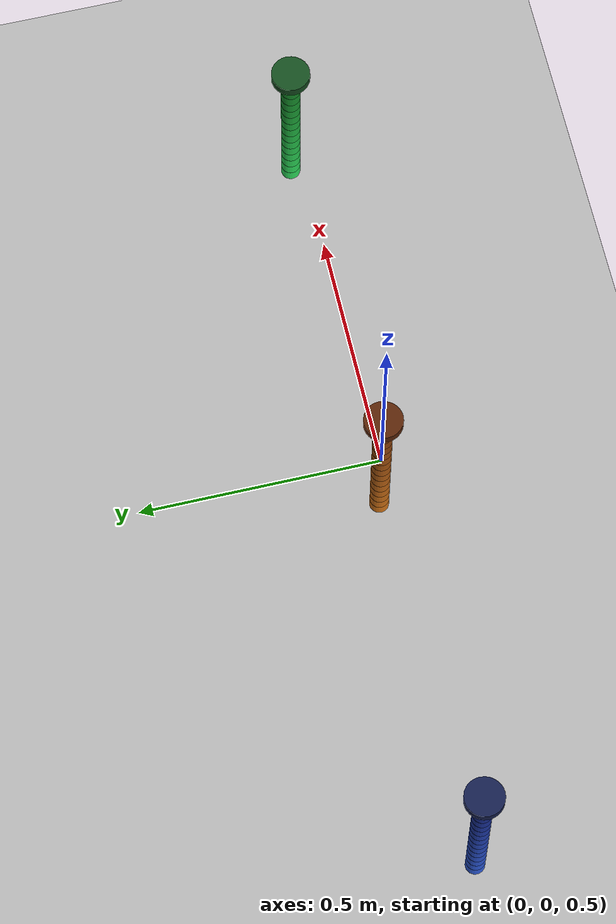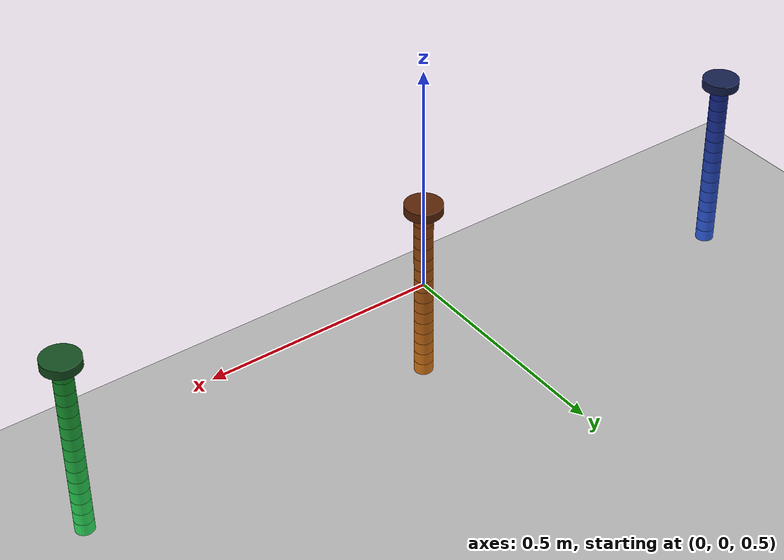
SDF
<?xml version="1.0" encoding="UTF-8"?>
<sdf version="1.9">
  <world name="continuum_arm_side_by_side">
    <physics type="ode">
      <max_step_size>0.001</max_step_size>
      <real_time_factor>1.0</real_time_factor>
      <real_time_update_rate>1000</real_time_update_rate>
    </physics>
    <plugin name="gz::sim::systems::Physics" filename="gz-sim-physics-system"/>
    <plugin name="gz::sim::systems::UserCommands" filename="gz-sim-user-commands-system"/>
    <plugin name="gz::sim::systems::SceneBroadcaster" filename="gz-sim-scene-broadcaster-system"/>
    <plugin filename="gz-sim-pose-publisher-system" name="gz::sim::systems::PosePublisher">
      <publish_link_pose>true</publish_link_pose>
      <publish_model_pose>true</publish_model_pose>
      <use_pose_vector_msg>true</use_pose_vector_msg>
      <static_publisher>false</static_publisher>
      <update_frequency>60</update_frequency>
    </plugin>

    <gravity>0 0 -9.8</gravity>

    <light name="sun" type="directional">
      <pose>0 0 10 0 0 0</pose>
      <direction>0.3 0.3 -0.9</direction>
      <diffuse>0.9 0.9 0.9 1</diffuse>
    </light>

    <gui fullscreen="false">
      <plugin filename="MinimalScene" name="3D View">
        <gz-gui>
          <title>3D View</title>
          <property type="bool" key="showTitleBar">false</property>
          <property type="string" key="state">docked</property>
        </gz-gui>
        <engine>ogre2</engine>
        <scene>scene</scene>
        <ambient_light>0.4 0.4 0.4</ambient_light>
        <background_color>0.8 0.8 0.8</background_color>
        <camera_pose>0 -2.6 0.85 0 0.2 1.5708</camera_pose>
        <camera_clip>
          <near>0.05</near>
          <far>5000</far>
        </camera_clip>
      </plugin>
      <plugin filename="InteractiveViewControl" name="Interactive view control">
        <gz-gui>
          <property key="resizable" type="bool">false</property>
          <property key="width" type="double">5</property>
          <property key="height" type="double">5</property>
          <property key="state" type="string">floating</property>
          <property key="showTitleBar" type="bool">false</property>
        </gz-gui>
      </plugin>
      <plugin filename="GzSceneManager" name="Scene Manager">
        <gz-gui>
          <property key="resizable" type="bool">false</property>
          <property key="width" type="double">5</property>
          <property key="height" type="double">5</property>
          <property key="state" type="string">floating</property>
          <property key="showTitleBar" type="bool">false</property>
        </gz-gui>
      </plugin>
      <plugin name="World control" filename="WorldControl">
        <gz-gui>
          <title>World control</title>
          <property type="bool" key="showTitleBar">0</property>
          <property type="bool" key="resizable">0</property>
          <property type="double" key="height">72</property>
          <property type="double" key="width">121</property>
          <property type="double" key="z">1</property>
          <property type="string" key="state">floating</property>
          <anchors target="3D View">
            <line own="left" target="left"/>
            <line own="bottom" target="bottom"/>
          </anchors>
        </gz-gui>
        <play_pause>1</play_pause>
        <step>1</step>
        <start_paused>0</start_paused>
      </plugin>
      <plugin name="World stats" filename="WorldStats">
        <gz-gui>
          <title>World stats</title>
          <property type="bool" key="showTitleBar">0</property>
          <property type="bool" key="resizable">0</property>
          <property type="double" key="height">110</property>
          <property type="double" key="width">290</property>
          <property type="double" key="z">1</property>
          <property type="string" key="state">floating</property>
          <anchors target="3D View">
            <line own="right" target="right"/>
            <line own="bottom" target="bottom"/>
          </anchors>
        </gz-gui>
        <sim_time>1</sim_time>
        <real_time>1</real_time>
        <real_time_factor>1</real_time_factor>
        <iterations>1</iterations>
      </plugin>
    </gui>

    <model name="ground_plane">
      <static>true</static>
      <link name="link">
        <collision name="collision">
          <geometry><plane><normal>0 0 1</normal><size>10 10</size></plane></geometry>
        </collision>
        <visual name="visual">
          <geometry><plane><normal>0 0 1</normal><size>10 10</size></plane></geometry>
          <material><ambient>0.7 0.7 0.7 1</ambient></material>
        </visual>
      </link>
    </model>

    <model name="continuum_arm_pcc_rig">
      <pose>-0.8 0 0.7 0 0 0</pose>
      <static>false</static>
      <include merge='true'>
        <uri>model://continuum_arm_pcc</uri>
      </include>
      <joint name="world_mount_joint" type="fixed">
        <parent>world</parent>
        <child>continuum_arm_pcc/base_cyl</child>
      </joint>
    </model>

    <model name="continuum_arm_cosserat_rig">
      <pose>0 0 0.7 0 0 0</pose>
      <static>false</static>
      <include merge='true'>
        <uri>model://continuum_arm_cosserat</uri>
      </include>
      <joint name="world_mount_joint" type="fixed">
        <parent>world</parent>
        <child>continuum_arm_cosserat/base_cyl</child>
      </joint>
    </model>

    <model name="continuum_arm_rbsn_rig">
      <pose>0.8 0 0.7 0 0 0</pose>
      <static>false</static>
      <include merge='true'>
        <uri>model://continuum_arm_rbsn</uri>
      </include>
      <joint name="world_mount_joint" type="fixed">
        <parent>world</parent>
        <child>continuum_arm_rbsn/base_cyl</child>
      </joint>
    </model>
  </world>
</sdf>

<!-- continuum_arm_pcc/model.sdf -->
<sdf version='1.9'>
  <model name='continuum_arm_pcc'>
    <self_collide>false</self_collide>
    <static>false</static>

    <link name="continuum_arm_pcc/base_cyl">
      <pose>0 0 -0.01000 0 0 0</pose>
      <gravity>true</gravity>
      <self_collide>false</self_collide>
      <velocity_decay/>
      <inertial>
        <mass>0.078431</mass>
        <inertia>
          <ixx>3.398693e-05</ixx>
          <iyy>3.398693e-05</iyy>
          <izz>6.274510e-05</izz>
        </inertia>
      </inertial>
      <collision name="continuum_arm_pcc/base_cyl_collision">
        <geometry>
          <cylinder><radius>0.04</radius><length>0.02</length></cylinder>
        </geometry>
      </collision>
      <visual name="continuum_arm_pcc/base_cyl_visual">
        <geometry>
          <cylinder><radius>0.04</radius><length>0.02</length></cylinder>
        </geometry>
        <material>
          <ambient>0.05 0.08 0.20 1</ambient>
          <diffuse>0.08 0.12 0.30 1</diffuse>
          <specular>0.2 0.2 0.2 1</specular>
        </material>
      </visual>
    </link>
    <!-- Segment 1/15 -->
    <link name="continuum_arm_pcc/segment_1">
      <pose>0 0 -0.03333 0 0 0</pose>
      <gravity>true</gravity>
      <self_collide>false</self_collide>
      <velocity_decay/>
      <inertial>
        <mass>0.011438</mass>
        <inertia>
          <ixx>2.464975e-06</ixx>
          <iyy>2.464975e-06</iyy>
          <izz>3.574346e-06</izz>
        </inertia>
      </inertial>
      <collision name="continuum_arm_pcc/segment_1_collision">
        <geometry>
          <cylinder><radius>0.02</radius><length>0.02666666666666667</length></cylinder>
        </geometry>
      </collision>
      <visual name="continuum_arm_pcc/segment_1_visual">
        <geometry>
          <cylinder><radius>0.02</radius><length>0.02666666666666667</length></cylinder>
        </geometry>
        <material>
          <ambient>0.050 0.080 0.350 1</ambient>
          <diffuse>0.080 0.150 0.550 1</diffuse>
          <specular>0.2 0.2 0.2 1</specular>
        </material>
      </visual>
    </link>
    <joint name="continuum_arm_pcc/joint_1" type="universal">
      <parent>continuum_arm_pcc/base_cyl</parent>
      <child>continuum_arm_pcc/segment_1</child>
      <pose>0 0 0.01333 0 0 0</pose>
      <axis>
        <xyz>1 0 0</xyz>
        <limit>
          <lower>-0.8</lower>
          <upper>0.8</upper>
          <effort>0.24</effort>
          <velocity>5.0</velocity>
        </limit>
        <dynamics>
          <spring_stiffness>1.61068</spring_stiffness>
          <spring_reference>0.0</spring_reference>
          <damping>0.08</damping>
        </dynamics>
      </axis>
      <axis2>
        <xyz>0 1 0</xyz>
        <limit>
          <lower>-0.8</lower>
          <upper>0.8</upper>
          <effort>0.24</effort>
          <velocity>5.0</velocity>
        </limit>
        <dynamics>
          <spring_stiffness>1.61068</spring_stiffness>
          <spring_reference>0.0</spring_reference>
          <damping>0.08</damping>
        </dynamics>
      </axis2>
    </joint>
    <!-- Segment 2/15 -->
    <link name="continuum_arm_pcc/segment_2">
      <pose>0 0 -0.06000 0 0 0</pose>
      <gravity>true</gravity>
      <self_collide>false</self_collide>
      <velocity_decay/>
      <inertial>
        <mass>0.011438</mass>
        <inertia>
          <ixx>2.464975e-06</ixx>
          <iyy>2.464975e-06</iyy>
          <izz>3.574346e-06</izz>
        </inertia>
      </inertial>
      <collision name="continuum_arm_pcc/segment_2_collision">
        <geometry>
          <cylinder><radius>0.02</radius><length>0.02666666666666667</length></cylinder>
        </geometry>
      </collision>
      <visual name="continuum_arm_pcc/segment_2_visual">
        <geometry>
          <cylinder><radius>0.02</radius><length>0.02666666666666667</length></cylinder>
        </geometry>
        <material>
          <ambient>0.057 0.093 0.382 1</ambient>
          <diffuse>0.089 0.168 0.579 1</diffuse>
          <specular>0.2 0.2 0.2 1</specular>
        </material>
      </visual>
    </link>
    <joint name="continuum_arm_pcc/joint_2" type="universal">
      <parent>continuum_arm_pcc/segment_1</parent>
      <child>continuum_arm_pcc/segment_2</child>
      <pose>0 0 0.01333 0 0 0</pose>
      <axis>
        <xyz>1 0 0</xyz>
        <limit>
          <lower>-0.8</lower>
          <upper>0.8</upper>
          <effort>0.24</effort>
          <velocity>5.0</velocity>
        </limit>
        <dynamics>
          <spring_stiffness>1.61068</spring_stiffness>
          <spring_reference>0.0</spring_reference>
          <damping>0.08</damping>
        </dynamics>
      </axis>
      <axis2>
        <xyz>0 1 0</xyz>
        <limit>
          <lower>-0.8</lower>
          <upper>0.8</upper>
          <effort>0.24</effort>
          <velocity>5.0</velocity>
        </limit>
        <dynamics>
          <spring_stiffness>1.61068</spring_stiffness>
          <spring_reference>0.0</spring_reference>
          <damping>0.08</damping>
        </dynamics>
      </axis2>
    </joint>
    <!-- Segment 3/15 -->
    <link name="continuum_arm_pcc/segment_3">
      <pose>0 0 -0.08667 0 0 0</pose>
      <gravity>true</gravity>
      <self_collide>false</self_collide>
      <velocity_decay/>
      <inertial>
        <mass>0.011438</mass>
        <inertia>
          <ixx>2.464975e-06</ixx>
          <iyy>2.464975e-06</iyy>
          <izz>3.574346e-06</izz>
        </inertia>
      </inertial>
      <collision name="continuum_arm_pcc/segment_3_collision">
        <geometry>
          <cylinder><radius>0.02</radius><length>0.02666666666666667</length></cylinder>
        </geometry>
      </collision>
      <visual name="continuum_arm_pcc/segment_3_visual">
        <geometry>
          <cylinder><radius>0.02</radius><length>0.02666666666666667</length></cylinder>
        </geometry>
        <material>
          <ambient>0.064 0.106 0.414 1</ambient>
          <diffuse>0.097 0.186 0.607 1</diffuse>
          <specular>0.2 0.2 0.2 1</specular>
        </material>
      </visual>
    </link>
    <joint name="continuum_arm_pcc/joint_3" type="universal">
      <parent>continuum_arm_pcc/segment_2</parent>
      <child>continuum_arm_pcc/segment_3</child>
      <pose>0 0 0.01333 0 0 0</pose>
      <axis>
        <xyz>1 0 0</xyz>
        <limit>
          <lower>-0.8</lower>
          <upper>0.8</upper>
          <effort>0.24</effort>
          <velocity>5.0</velocity>
        </limit>
        <dynamics>
          <spring_stiffness>1.61068</spring_stiffness>
          <spring_reference>0.0</spring_reference>
          <damping>0.08</damping>
        </dynamics>
      </axis>
      <axis2>
        <xyz>0 1 0</xyz>
        <limit>
          <lower>-0.8</lower>
          <upper>0.8</upper>
          <effort>0.24</effort>
          <velocity>5.0</velocity>
        </limit>
        <dynamics>
          <spring_stiffness>1.61068</spring_stiffness>
          <spring_reference>0.0</spring_reference>
          <damping>0.08</damping>
        </dynamics>
      </axis2>
    </joint>
    <!-- Segment 4/15 -->
    <link name="continuum_arm_pcc/segment_4">
      <pose>0 0 -0.11333 0 0 0</pose>
      <gravity>true</gravity>
      <self_collide>false</self_collide>
      <velocity_decay/>
      <inertial>
        <mass>0.011438</mass>
        <inertia>
          <ixx>2.464975e-06</ixx>
          <iyy>2.464975e-06</iyy>
          <izz>3.574346e-06</izz>
        </inertia>
      </inertial>
      <collision name="continuum_arm_pcc/segment_4_collision">
        <geometry>
          <cylinder><radius>0.02</radius><length>0.02666666666666667</length></cylinder>
        </geometry>
      </collision>
      <visual name="continuum_arm_pcc/segment_4_visual">
        <geometry>
          <cylinder><radius>0.02</radius><length>0.02666666666666667</length></cylinder>
        </geometry>
        <material>
          <ambient>0.071 0.119 0.446 1</ambient>
          <diffuse>0.106 0.204 0.636 1</diffuse>
          <specular>0.2 0.2 0.2 1</specular>
        </material>
      </visual>
    </link>
    <joint name="continuum_arm_pcc/joint_4" type="universal">
      <parent>continuum_arm_pcc/segment_3</parent>
      <child>continuum_arm_pcc/segment_4</child>
      <pose>0 0 0.01333 0 0 0</pose>
      <axis>
        <xyz>1 0 0</xyz>
        <limit>
          <lower>-0.8</lower>
          <upper>0.8</upper>
          <effort>0.24</effort>
          <velocity>5.0</velocity>
        </limit>
        <dynamics>
          <spring_stiffness>1.61068</spring_stiffness>
          <spring_reference>0.0</spring_reference>
          <damping>0.08</damping>
        </dynamics>
      </axis>
      <axis2>
        <xyz>0 1 0</xyz>
        <limit>
          <lower>-0.8</lower>
          <upper>0.8</upper>
          <effort>0.24</effort>
          <velocity>5.0</velocity>
        </limit>
        <dynamics>
          <spring_stiffness>1.61068</spring_stiffness>
          <spring_reference>0.0</spring_reference>
          <damping>0.08</damping>
        </dynamics>
      </axis2>
    </joint>
    <!-- Segment 5/15 -->
    <link name="continuum_arm_pcc/segment_5">
      <pose>0 0 -0.14000 0 0 0</pose>
      <gravity>true</gravity>
      <self_collide>false</self_collide>
      <velocity_decay/>
      <inertial>
        <mass>0.011438</mass>
        <inertia>
          <ixx>2.464975e-06</ixx>
          <iyy>2.464975e-06</iyy>
          <izz>3.574346e-06</izz>
        </inertia>
      </inertial>
      <collision name="continuum_arm_pcc/segment_5_collision">
        <geometry>
          <cylinder><radius>0.02</radius><length>0.02666666666666667</length></cylinder>
        </geometry>
      </collision>
      <visual name="continuum_arm_pcc/segment_5_visual">
        <geometry>
          <cylinder><radius>0.02</radius><length>0.02666666666666667</length></cylinder>
        </geometry>
        <material>
          <ambient>0.079 0.131 0.479 1</ambient>
          <diffuse>0.114 0.221 0.664 1</diffuse>
          <specular>0.2 0.2 0.2 1</specular>
        </material>
      </visual>
    </link>
    <joint name="continuum_arm_pcc/joint_5" type="universal">
      <parent>continuum_arm_pcc/segment_4</parent>
      <child>continuum_arm_pcc/segment_5</child>
      <pose>0 0 0.01333 0 0 0</pose>
      <axis>
        <xyz>1 0 0</xyz>
        <limit>
          <lower>-0.8</lower>
          <upper>0.8</upper>
          <effort>0.24</effort>
          <velocity>5.0</velocity>
        </limit>
        <dynamics>
          <spring_stiffness>1.61068</spring_stiffness>
          <spring_reference>0.0</spring_reference>
          <damping>0.08</damping>
        </dynamics>
      </axis>
      <axis2>
        <xyz>0 1 0</xyz>
        <limit>
          <lower>-0.8</lower>
          <upper>0.8</upper>
          <effort>0.24</effort>
          <velocity>5.0</velocity>
        </limit>
        <dynamics>
          <spring_stiffness>1.61068</spring_stiffness>
          <spring_reference>0.0</spring_reference>
          <damping>0.08</damping>
        </dynamics>
      </axis2>
    </joint>
    <!-- Segment 6/15 -->
    <link name="continuum_arm_pcc/segment_6">
      <pose>0 0 -0.16667 0 0 0</pose>
      <gravity>true</gravity>
      <self_collide>false</self_collide>
      <velocity_decay/>
      <inertial>
        <mass>0.011438</mass>
        <inertia>
          <ixx>2.464975e-06</ixx>
          <iyy>2.464975e-06</iyy>
          <izz>3.574346e-06</izz>
        </inertia>
      </inertial>
      <collision name="continuum_arm_pcc/segment_6_collision">
        <geometry>
          <cylinder><radius>0.02</radius><length>0.02666666666666667</length></cylinder>
        </geometry>
      </collision>
      <visual name="continuum_arm_pcc/segment_6_visual">
        <geometry>
          <cylinder><radius>0.02</radius><length>0.02666666666666667</length></cylinder>
        </geometry>
        <material>
          <ambient>0.086 0.144 0.511 1</ambient>
          <diffuse>0.123 0.239 0.693 1</diffuse>
          <specular>0.2 0.2 0.2 1</specular>
        </material>
      </visual>
    </link>
    <joint name="continuum_arm_pcc/joint_6" type="universal">
      <parent>continuum_arm_pcc/segment_5</parent>
      <child>continuum_arm_pcc/segment_6</child>
      <pose>0 0 0.01333 0 0 0</pose>
      <axis>
        <xyz>1 0 0</xyz>
        <limit>
          <lower>-0.8</lower>
          <upper>0.8</upper>
          <effort>0.24</effort>
          <velocity>5.0</velocity>
        </limit>
        <dynamics>
          <spring_stiffness>1.61068</spring_stiffness>
          <spring_reference>0.0</spring_reference>
          <damping>0.08</damping>
        </dynamics>
      </axis>
      <axis2>
        <xyz>0 1 0</xyz>
        <limit>
          <lower>-0.8</lower>
          <upper>0.8</upper>
          <effort>0.24</effort>
          <velocity>5.0</velocity>
        </limit>
        <dynamics>
          <spring_stiffness>1.61068</spring_stiffness>
          <spring_reference>0.0</spring_reference>
          <damping>0.08</damping>
        </dynamics>
      </axis2>
    </joint>
    <!-- Segment 7/15 -->
    <link name="continuum_arm_pcc/segment_7">
      <pose>0 0 -0.19333 0 0 0</pose>
      <gravity>true</gravity>
      <self_collide>false</self_collide>
      <velocity_decay/>
      <inertial>
        <mass>0.011438</mass>
        <inertia>
          <ixx>2.464975e-06</ixx>
          <iyy>2.464975e-06</iyy>
          <izz>3.574346e-06</izz>
        </inertia>
      </inertial>
      <collision name="continuum_arm_pcc/segment_7_collision">
        <geometry>
          <cylinder><radius>0.02</radius><length>0.02666666666666667</length></cylinder>
        </geometry>
      </collision>
      <visual name="continuum_arm_pcc/segment_7_visual">
        <geometry>
          <cylinder><radius>0.02</radius><length>0.02666666666666667</length></cylinder>
        </geometry>
        <material>
          <ambient>0.093 0.157 0.543 1</ambient>
          <diffuse>0.131 0.257 0.721 1</diffuse>
          <specular>0.2 0.2 0.2 1</specular>
        </material>
      </visual>
    </link>
    <joint name="continuum_arm_pcc/joint_7" type="universal">
      <parent>continuum_arm_pcc/segment_6</parent>
      <child>continuum_arm_pcc/segment_7</child>
      <pose>0 0 0.01333 0 0 0</pose>
      <axis>
        <xyz>1 0 0</xyz>
        <limit>
          <lower>-0.8</lower>
          <upper>0.8</upper>
          <effort>0.24</effort>
          <velocity>5.0</velocity>
        </limit>
        <dynamics>
          <spring_stiffness>1.61068</spring_stiffness>
          <spring_reference>0.0</spring_reference>
          <damping>0.08</damping>
        </dynamics>
      </axis>
      <axis2>
        <xyz>0 1 0</xyz>
        <limit>
          <lower>-0.8</lower>
          <upper>0.8</upper>
          <effort>0.24</effort>
          <velocity>5.0</velocity>
        </limit>
        <dynamics>
          <spring_stiffness>1.61068</spring_stiffness>
          <spring_reference>0.0</spring_reference>
          <damping>0.08</damping>
        </dynamics>
      </axis2>
    </joint>
    <!-- Segment 8/15 -->
    <link name="continuum_arm_pcc/segment_8">
      <pose>0 0 -0.22000 0 0 0</pose>
      <gravity>true</gravity>
      <self_collide>false</self_collide>
      <velocity_decay/>
      <inertial>
        <mass>0.011438</mass>
        <inertia>
          <ixx>2.464975e-06</ixx>
          <iyy>2.464975e-06</iyy>
          <izz>3.574346e-06</izz>
        </inertia>
      </inertial>
      <collision name="continuum_arm_pcc/segment_8_collision">
        <geometry>
          <cylinder><radius>0.02</radius><length>0.02666666666666667</length></cylinder>
        </geometry>
      </collision>
      <visual name="continuum_arm_pcc/segment_8_visual">
        <geometry>
          <cylinder><radius>0.02</radius><length>0.02666666666666667</length></cylinder>
        </geometry>
        <material>
          <ambient>0.100 0.170 0.575 1</ambient>
          <diffuse>0.140 0.275 0.750 1</diffuse>
          <specular>0.2 0.2 0.2 1</specular>
        </material>
      </visual>
    </link>
    <joint name="continuum_arm_pcc/joint_8" type="universal">
      <parent>continuum_arm_pcc/segment_7</parent>
      <child>continuum_arm_pcc/segment_8</child>
      <pose>0 0 0.01333 0 0 0</pose>
      <axis>
        <xyz>1 0 0</xyz>
        <limit>
          <lower>-0.8</lower>
          <upper>0.8</upper>
          <effort>0.24</effort>
          <velocity>5.0</velocity>
        </limit>
        <dynamics>
          <spring_stiffness>1.61068</spring_stiffness>
          <spring_reference>0.0</spring_reference>
          <damping>0.08</damping>
        </dynamics>
      </axis>
      <axis2>
        <xyz>0 1 0</xyz>
        <limit>
          <lower>-0.8</lower>
          <upper>0.8</upper>
          <effort>0.24</effort>
          <velocity>5.0</velocity>
        </limit>
        <dynamics>
          <spring_stiffness>1.61068</spring_stiffness>
          <spring_reference>0.0</spring_reference>
          <damping>0.08</damping>
        </dynamics>
      </axis2>
    </joint>
    <!-- Segment 9/15 -->
    <link name="continuum_arm_pcc/segment_9">
      <pose>0 0 -0.24667 0 0 0</pose>
      <gravity>true</gravity>
      <self_collide>false</self_collide>
      <velocity_decay/>
      <inertial>
        <mass>0.011438</mass>
        <inertia>
          <ixx>2.464975e-06</ixx>
          <iyy>2.464975e-06</iyy>
          <izz>3.574346e-06</izz>
        </inertia>
      </inertial>
      <collision name="continuum_arm_pcc/segment_9_collision">
        <geometry>
          <cylinder><radius>0.02</radius><length>0.02666666666666667</length></cylinder>
        </geometry>
      </collision>
      <visual name="continuum_arm_pcc/segment_9_visual">
        <geometry>
          <cylinder><radius>0.02</radius><length>0.02666666666666667</length></cylinder>
        </geometry>
        <material>
          <ambient>0.107 0.183 0.607 1</ambient>
          <diffuse>0.149 0.293 0.779 1</diffuse>
          <specular>0.2 0.2 0.2 1</specular>
        </material>
      </visual>
    </link>
    <joint name="continuum_arm_pcc/joint_9" type="universal">
      <parent>continuum_arm_pcc/segment_8</parent>
      <child>continuum_arm_pcc/segment_9</child>
      <pose>0 0 0.01333 0 0 0</pose>
      <axis>
        <xyz>1 0 0</xyz>
        <limit>
          <lower>-0.8</lower>
          <upper>0.8</upper>
          <effort>0.24</effort>
          <velocity>5.0</velocity>
        </limit>
        <dynamics>
          <spring_stiffness>1.61068</spring_stiffness>
          <spring_reference>0.0</spring_reference>
          <damping>0.08</damping>
        </dynamics>
      </axis>
      <axis2>
        <xyz>0 1 0</xyz>
        <limit>
          <lower>-0.8</lower>
          <upper>0.8</upper>
          <effort>0.24</effort>
          <velocity>5.0</velocity>
        </limit>
        <dynamics>
          <spring_stiffness>1.61068</spring_stiffness>
          <spring_reference>0.0</spring_reference>
          <damping>0.08</damping>
        </dynamics>
      </axis2>
    </joint>
    <!-- Segment 10/15 -->
    <link name="continuum_arm_pcc/segment_10">
      <pose>0 0 -0.27333 0 0 0</pose>
      <gravity>true</gravity>
      <self_collide>false</self_collide>
      <velocity_decay/>
      <inertial>
        <mass>0.011438</mass>
        <inertia>
          <ixx>2.464975e-06</ixx>
          <iyy>2.464975e-06</iyy>
          <izz>3.574346e-06</izz>
        </inertia>
      </inertial>
      <collision name="continuum_arm_pcc/segment_10_collision">
        <geometry>
          <cylinder><radius>0.02</radius><length>0.02666666666666667</length></cylinder>
        </geometry>
      </collision>
      <visual name="continuum_arm_pcc/segment_10_visual">
        <geometry>
          <cylinder><radius>0.02</radius><length>0.02666666666666667</length></cylinder>
        </geometry>
        <material>
          <ambient>0.114 0.196 0.639 1</ambient>
          <diffuse>0.157 0.311 0.807 1</diffuse>
          <specular>0.2 0.2 0.2 1</specular>
        </material>
      </visual>
    </link>
    <joint name="continuum_arm_pcc/joint_10" type="universal">
      <parent>continuum_arm_pcc/segment_9</parent>
      <child>continuum_arm_pcc/segment_10</child>
      <pose>0 0 0.01333 0 0 0</pose>
      <axis>
        <xyz>1 0 0</xyz>
        <limit>
          <lower>-0.8</lower>
          <upper>0.8</upper>
          <effort>0.24</effort>
          <velocity>5.0</velocity>
        </limit>
        <dynamics>
          <spring_stiffness>1.61068</spring_stiffness>
          <spring_reference>0.0</spring_reference>
          <damping>0.08</damping>
        </dynamics>
      </axis>
      <axis2>
        <xyz>0 1 0</xyz>
        <limit>
          <lower>-0.8</lower>
          <upper>0.8</upper>
          <effort>0.24</effort>
          <velocity>5.0</velocity>
        </limit>
        <dynamics>
          <spring_stiffness>1.61068</spring_stiffness>
          <spring_reference>0.0</spring_reference>
          <damping>0.08</damping>
        </dynamics>
      </axis2>
    </joint>
    <!-- Segment 11/15 -->
    <link name="continuum_arm_pcc/segment_11">
      <pose>0 0 -0.30000 0 0 0</pose>
      <gravity>true</gravity>
      <self_collide>false</self_collide>
      <velocity_decay/>
      <inertial>
        <mass>0.011438</mass>
        <inertia>
          <ixx>2.464975e-06</ixx>
          <iyy>2.464975e-06</iyy>
          <izz>3.574346e-06</izz>
        </inertia>
      </inertial>
      <collision name="continuum_arm_pcc/segment_11_collision">
        <geometry>
          <cylinder><radius>0.02</radius><length>0.02666666666666667</length></cylinder>
        </geometry>
      </collision>
      <visual name="continuum_arm_pcc/segment_11_visual">
        <geometry>
          <cylinder><radius>0.02</radius><length>0.02666666666666667</length></cylinder>
        </geometry>
        <material>
          <ambient>0.121 0.209 0.671 1</ambient>
          <diffuse>0.166 0.329 0.836 1</diffuse>
          <specular>0.2 0.2 0.2 1</specular>
        </material>
      </visual>
    </link>
    <joint name="continuum_arm_pcc/joint_11" type="universal">
      <parent>continuum_arm_pcc/segment_10</parent>
      <child>continuum_arm_pcc/segment_11</child>
      <pose>0 0 0.01333 0 0 0</pose>
      <axis>
        <xyz>1 0 0</xyz>
        <limit>
          <lower>-0.8</lower>
          <upper>0.8</upper>
          <effort>0.24</effort>
          <velocity>5.0</velocity>
        </limit>
        <dynamics>
          <spring_stiffness>1.61068</spring_stiffness>
          <spring_reference>0.0</spring_reference>
          <damping>0.08</damping>
        </dynamics>
      </axis>
      <axis2>
        <xyz>0 1 0</xyz>
        <limit>
          <lower>-0.8</lower>
          <upper>0.8</upper>
          <effort>0.24</effort>
          <velocity>5.0</velocity>
        </limit>
        <dynamics>
          <spring_stiffness>1.61068</spring_stiffness>
          <spring_reference>0.0</spring_reference>
          <damping>0.08</damping>
        </dynamics>
      </axis2>
    </joint>
    <!-- Segment 12/15 -->
    <link name="continuum_arm_pcc/segment_12">
      <pose>0 0 -0.32667 0 0 0</pose>
      <gravity>true</gravity>
      <self_collide>false</self_collide>
      <velocity_decay/>
      <inertial>
        <mass>0.011438</mass>
        <inertia>
          <ixx>2.464975e-06</ixx>
          <iyy>2.464975e-06</iyy>
          <izz>3.574346e-06</izz>
        </inertia>
      </inertial>
      <collision name="continuum_arm_pcc/segment_12_collision">
        <geometry>
          <cylinder><radius>0.02</radius><length>0.02666666666666667</length></cylinder>
        </geometry>
      </collision>
      <visual name="continuum_arm_pcc/segment_12_visual">
        <geometry>
          <cylinder><radius>0.02</radius><length>0.02666666666666667</length></cylinder>
        </geometry>
        <material>
          <ambient>0.129 0.221 0.704 1</ambient>
          <diffuse>0.174 0.346 0.864 1</diffuse>
          <specular>0.2 0.2 0.2 1</specular>
        </material>
      </visual>
    </link>
    <joint name="continuum_arm_pcc/joint_12" type="universal">
      <parent>continuum_arm_pcc/segment_11</parent>
      <child>continuum_arm_pcc/segment_12</child>
      <pose>0 0 0.01333 0 0 0</pose>
      <axis>
        <xyz>1 0 0</xyz>
        <limit>
          <lower>-0.8</lower>
          <upper>0.8</upper>
          <effort>0.24</effort>
          <velocity>5.0</velocity>
        </limit>
        <dynamics>
          <spring_stiffness>1.61068</spring_stiffness>
          <spring_reference>0.0</spring_reference>
          <damping>0.08</damping>
        </dynamics>
      </axis>
      <axis2>
        <xyz>0 1 0</xyz>
        <limit>
          <lower>-0.8</lower>
          <upper>0.8</upper>
          <effort>0.24</effort>
          <velocity>5.0</velocity>
        </limit>
        <dynamics>
          <spring_stiffness>1.61068</spring_stiffness>
          <spring_reference>0.0</spring_reference>
          <damping>0.08</damping>
        </dynamics>
      </axis2>
    </joint>
    <!-- Segment 13/15 -->
    <link name="continuum_arm_pcc/segment_13">
      <pose>0 0 -0.35333 0 0 0</pose>
      <gravity>true</gravity>
      <self_collide>false</self_collide>
      <velocity_decay/>
      <inertial>
        <mass>0.011438</mass>
        <inertia>
          <ixx>2.464975e-06</ixx>
          <iyy>2.464975e-06</iyy>
          <izz>3.574346e-06</izz>
        </inertia>
      </inertial>
      <collision name="continuum_arm_pcc/segment_13_collision">
        <geometry>
          <cylinder><radius>0.02</radius><length>0.02666666666666667</length></cylinder>
        </geometry>
      </collision>
      <visual name="continuum_arm_pcc/segment_13_visual">
        <geometry>
          <cylinder><radius>0.02</radius><length>0.02666666666666667</length></cylinder>
        </geometry>
        <material>
          <ambient>0.136 0.234 0.736 1</ambient>
          <diffuse>0.183 0.364 0.893 1</diffuse>
          <specular>0.2 0.2 0.2 1</specular>
        </material>
      </visual>
    </link>
    <joint name="continuum_arm_pcc/joint_13" type="universal">
      <parent>continuum_arm_pcc/segment_12</parent>
      <child>continuum_arm_pcc/segment_13</child>
      <pose>0 0 0.01333 0 0 0</pose>
      <axis>
        <xyz>1 0 0</xyz>
        <limit>
          <lower>-0.8</lower>
          <upper>0.8</upper>
          <effort>0.24</effort>
          <velocity>5.0</velocity>
        </limit>
        <dynamics>
          <spring_stiffness>1.61068</spring_stiffness>
          <spring_reference>0.0</spring_reference>
          <damping>0.08</damping>
        </dynamics>
      </axis>
      <axis2>
        <xyz>0 1 0</xyz>
        <limit>
          <lower>-0.8</lower>
          <upper>0.8</upper>
          <effort>0.24</effort>
          <velocity>5.0</velocity>
        </limit>
        <dynamics>
          <spring_stiffness>1.61068</spring_stiffness>
          <spring_reference>0.0</spring_reference>
          <damping>0.08</damping>
        </dynamics>
      </axis2>
    </joint>
    <!-- Segment 14/15 -->
    <link name="continuum_arm_pcc/segment_14">
      <pose>0 0 -0.38000 0 0 0</pose>
      <gravity>true</gravity>
      <self_collide>false</self_collide>
      <velocity_decay/>
      <inertial>
        <mass>0.011438</mass>
        <inertia>
          <ixx>2.464975e-06</ixx>
          <iyy>2.464975e-06</iyy>
          <izz>3.574346e-06</izz>
        </inertia>
      </inertial>
      <collision name="continuum_arm_pcc/segment_14_collision">
        <geometry>
          <cylinder><radius>0.02</radius><length>0.02666666666666667</length></cylinder>
        </geometry>
      </collision>
      <visual name="continuum_arm_pcc/segment_14_visual">
        <geometry>
          <cylinder><radius>0.02</radius><length>0.02666666666666667</length></cylinder>
        </geometry>
        <material>
          <ambient>0.143 0.247 0.768 1</ambient>
          <diffuse>0.191 0.382 0.921 1</diffuse>
          <specular>0.2 0.2 0.2 1</specular>
        </material>
      </visual>
    </link>
    <joint name="continuum_arm_pcc/joint_14" type="universal">
      <parent>continuum_arm_pcc/segment_13</parent>
      <child>continuum_arm_pcc/segment_14</child>
      <pose>0 0 0.01333 0 0 0</pose>
      <axis>
        <xyz>1 0 0</xyz>
        <limit>
          <lower>-0.8</lower>
          <upper>0.8</upper>
          <effort>0.24</effort>
          <velocity>5.0</velocity>
        </limit>
        <dynamics>
          <spring_stiffness>1.61068</spring_stiffness>
          <spring_reference>0.0</spring_reference>
          <damping>0.08</damping>
        </dynamics>
      </axis>
      <axis2>
        <xyz>0 1 0</xyz>
        <limit>
          <lower>-0.8</lower>
          <upper>0.8</upper>
          <effort>0.24</effort>
          <velocity>5.0</velocity>
        </limit>
        <dynamics>
          <spring_stiffness>1.61068</spring_stiffness>
          <spring_reference>0.0</spring_reference>
          <damping>0.08</damping>
        </dynamics>
      </axis2>
    </joint>
    <!-- Segment 15/15 -->
    <link name="continuum_arm_pcc/segment_15">
      <pose>0 0 -0.40667 0 0 0</pose>
      <gravity>true</gravity>
      <self_collide>false</self_collide>
      <velocity_decay/>
      <inertial>
        <mass>0.011438</mass>
        <inertia>
          <ixx>2.464975e-06</ixx>
          <iyy>2.464975e-06</iyy>
          <izz>3.574346e-06</izz>
        </inertia>
      </inertial>
      <collision name="continuum_arm_pcc/segment_15_collision">
        <geometry>
          <cylinder><radius>0.02</radius><length>0.02666666666666667</length></cylinder>
        </geometry>
      </collision>
      <visual name="continuum_arm_pcc/segment_15_visual">
        <geometry>
          <cylinder><radius>0.02</radius><length>0.02666666666666667</length></cylinder>
        </geometry>
        <material>
          <ambient>0.150 0.260 0.800 1</ambient>
          <diffuse>0.200 0.400 0.950 1</diffuse>
          <specular>0.2 0.2 0.2 1</specular>
        </material>
      </visual>
    </link>
    <joint name="continuum_arm_pcc/joint_15" type="universal">
      <parent>continuum_arm_pcc/segment_14</parent>
      <child>continuum_arm_pcc/segment_15</child>
      <pose>0 0 0.01333 0 0 0</pose>
      <axis>
        <xyz>1 0 0</xyz>
        <limit>
          <lower>-0.8</lower>
          <upper>0.8</upper>
          <effort>0.24</effort>
          <velocity>5.0</velocity>
        </limit>
        <dynamics>
          <spring_stiffness>1.61068</spring_stiffness>
          <spring_reference>0.0</spring_reference>
          <damping>0.08</damping>
        </dynamics>
      </axis>
      <axis2>
        <xyz>0 1 0</xyz>
        <limit>
          <lower>-0.8</lower>
          <upper>0.8</upper>
          <effort>0.24</effort>
          <velocity>5.0</velocity>
        </limit>
        <dynamics>
          <spring_stiffness>1.61068</spring_stiffness>
          <spring_reference>0.0</spring_reference>
          <damping>0.08</damping>
        </dynamics>
      </axis2>
    </joint>

    <plugin filename="TendonArmController" name="tendon_arm_controller::TendonArmController">
      <joint_name>continuum_arm_pcc/joint_1</joint_name>
      <joint_name>continuum_arm_pcc/joint_2</joint_name>
      <joint_name>continuum_arm_pcc/joint_3</joint_name>
      <joint_name>continuum_arm_pcc/joint_4</joint_name>
      <joint_name>continuum_arm_pcc/joint_5</joint_name>
      <joint_name>continuum_arm_pcc/joint_6</joint_name>
      <joint_name>continuum_arm_pcc/joint_7</joint_name>
      <joint_name>continuum_arm_pcc/joint_8</joint_name>
      <joint_name>continuum_arm_pcc/joint_9</joint_name>
      <joint_name>continuum_arm_pcc/joint_10</joint_name>
      <joint_name>continuum_arm_pcc/joint_11</joint_name>
      <joint_name>continuum_arm_pcc/joint_12</joint_name>
      <joint_name>continuum_arm_pcc/joint_13</joint_name>
      <joint_name>continuum_arm_pcc/joint_14</joint_name>
      <joint_name>continuum_arm_pcc/joint_15</joint_name>
      <pitch_radius>0.015</pitch_radius>
      <rest_length>0.4</rest_length>
      <position_p_gain>5.0</position_p_gain>
      <position_d_gain>0.05</position_d_gain>
      <effort_limit>0.24</effort_limit>
      <tendon_topic>/continuum_arm_pcc/tendon_cmd</tendon_topic>
      <angles_topic>/continuum_arm_pcc/bend_angles</angles_topic>
      <command_filter_omega>2.92</command_filter_omega>
      <max_tendon_rate_m_s>0.06</max_tendon_rate_m_s>
    </plugin>

    <!-- Joint state feedback (actual, physics-integrated angles), same
         pattern rigid_arm_3link uses - lets the test script verify the arm
         actually bent the way the tendon command intended. -->
    <plugin filename="gz-sim-joint-state-publisher-system" name="gz::sim::systems::JointStatePublisher">
      <topic>/continuum_arm_pcc/joint_states</topic>
      <joint_name>continuum_arm_pcc/joint_1</joint_name>
      <joint_name>continuum_arm_pcc/joint_2</joint_name>
      <joint_name>continuum_arm_pcc/joint_3</joint_name>
      <joint_name>continuum_arm_pcc/joint_4</joint_name>
      <joint_name>continuum_arm_pcc/joint_5</joint_name>
      <joint_name>continuum_arm_pcc/joint_6</joint_name>
      <joint_name>continuum_arm_pcc/joint_7</joint_name>
      <joint_name>continuum_arm_pcc/joint_8</joint_name>
      <joint_name>continuum_arm_pcc/joint_9</joint_name>
      <joint_name>continuum_arm_pcc/joint_10</joint_name>
      <joint_name>continuum_arm_pcc/joint_11</joint_name>
      <joint_name>continuum_arm_pcc/joint_12</joint_name>
      <joint_name>continuum_arm_pcc/joint_13</joint_name>
      <joint_name>continuum_arm_pcc/joint_14</joint_name>
      <joint_name>continuum_arm_pcc/joint_15</joint_name>
    </plugin>

  </model>
</sdf>

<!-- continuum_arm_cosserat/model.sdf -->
<sdf version='1.9'>
  <model name='continuum_arm_cosserat'>
    <self_collide>false</self_collide>
    <static>false</static>

    <link name="continuum_arm_cosserat/base_cyl">
      <pose>0 0 -0.01000 0 0 0</pose>
      <gravity>true</gravity>
      <self_collide>false</self_collide>
      <velocity_decay/>
      <inertial>
        <mass>0.078431</mass>
        <inertia>
          <ixx>3.398693e-05</ixx>
          <iyy>3.398693e-05</iyy>
          <izz>6.274510e-05</izz>
        </inertia>
      </inertial>
      <collision name="continuum_arm_cosserat/base_cyl_collision">
        <geometry>
          <cylinder><radius>0.04</radius><length>0.02</length></cylinder>
        </geometry>
      </collision>
      <visual name="continuum_arm_cosserat/base_cyl_visual">
        <geometry>
          <cylinder><radius>0.04</radius><length>0.02</length></cylinder>
        </geometry>
        <material>
          <ambient>0.20 0.08 0.02 1</ambient>
          <diffuse>0.35 0.14 0.03 1</diffuse>
          <specular>0.2 0.2 0.2 1</specular>
        </material>
      </visual>
    </link>
    <!-- Segment 1/15 -->
    <link name="continuum_arm_cosserat/segment_1">
      <pose>0 0 -0.03333 0 0 0</pose>
      <gravity>true</gravity>
      <self_collide>false</self_collide>
      <velocity_decay/>
      <inertial>
        <mass>0.011438</mass>
        <inertia>
          <ixx>2.464975e-06</ixx>
          <iyy>2.464975e-06</iyy>
          <izz>3.574346e-06</izz>
        </inertia>
      </inertial>
      <collision name="continuum_arm_cosserat/segment_1_collision">
        <geometry>
          <cylinder><radius>0.02</radius><length>0.02666666666666667</length></cylinder>
        </geometry>
      </collision>
      <visual name="continuum_arm_cosserat/segment_1_visual">
        <geometry>
          <cylinder><radius>0.02</radius><length>0.02666666666666667</length></cylinder>
        </geometry>
        <material>
          <ambient>0.350 0.150 0.020 1</ambient>
          <diffuse>0.550 0.250 0.050 1</diffuse>
          <specular>0.2 0.2 0.2 1</specular>
        </material>
      </visual>
    </link>
    <joint name="continuum_arm_cosserat/joint_1" type="universal">
      <parent>continuum_arm_cosserat/base_cyl</parent>
      <child>continuum_arm_cosserat/segment_1</child>
      <pose>0 0 0.01333 0 0 0</pose>
      <axis>
        <xyz>1 0 0</xyz>
        <limit>
          <lower>-0.8</lower>
          <upper>0.8</upper>
          <effort>0.24</effort>
          <velocity>5.0</velocity>
        </limit>
        <dynamics>
          <damping>0.08</damping>
        </dynamics>
      </axis>
      <axis2>
        <xyz>0 1 0</xyz>
        <limit>
          <lower>-0.8</lower>
          <upper>0.8</upper>
          <effort>0.24</effort>
          <velocity>5.0</velocity>
        </limit>
        <dynamics>
          <damping>0.08</damping>
        </dynamics>
      </axis2>
    </joint>
    <!-- Segment 2/15 -->
    <link name="continuum_arm_cosserat/segment_2">
      <pose>0 0 -0.06000 0 0 0</pose>
      <gravity>true</gravity>
      <self_collide>false</self_collide>
      <velocity_decay/>
      <inertial>
        <mass>0.011438</mass>
        <inertia>
          <ixx>2.464975e-06</ixx>
          <iyy>2.464975e-06</iyy>
          <izz>3.574346e-06</izz>
        </inertia>
      </inertial>
      <collision name="continuum_arm_cosserat/segment_2_collision">
        <geometry>
          <cylinder><radius>0.02</radius><length>0.02666666666666667</length></cylinder>
        </geometry>
      </collision>
      <visual name="continuum_arm_cosserat/segment_2_visual">
        <geometry>
          <cylinder><radius>0.02</radius><length>0.02666666666666667</length></cylinder>
        </geometry>
        <material>
          <ambient>0.382 0.164 0.021 1</ambient>
          <diffuse>0.575 0.268 0.054 1</diffuse>
          <specular>0.2 0.2 0.2 1</specular>
        </material>
      </visual>
    </link>
    <joint name="continuum_arm_cosserat/joint_2" type="universal">
      <parent>continuum_arm_cosserat/segment_1</parent>
      <child>continuum_arm_cosserat/segment_2</child>
      <pose>0 0 0.01333 0 0 0</pose>
      <axis>
        <xyz>1 0 0</xyz>
        <limit>
          <lower>-0.8</lower>
          <upper>0.8</upper>
          <effort>0.24</effort>
          <velocity>5.0</velocity>
        </limit>
        <dynamics>
          <damping>0.08</damping>
        </dynamics>
      </axis>
      <axis2>
        <xyz>0 1 0</xyz>
        <limit>
          <lower>-0.8</lower>
          <upper>0.8</upper>
          <effort>0.24</effort>
          <velocity>5.0</velocity>
        </limit>
        <dynamics>
          <damping>0.08</damping>
        </dynamics>
      </axis2>
    </joint>
    <!-- Segment 3/15 -->
    <link name="continuum_arm_cosserat/segment_3">
      <pose>0 0 -0.08667 0 0 0</pose>
      <gravity>true</gravity>
      <self_collide>false</self_collide>
      <velocity_decay/>
      <inertial>
        <mass>0.011438</mass>
        <inertia>
          <ixx>2.464975e-06</ixx>
          <iyy>2.464975e-06</iyy>
          <izz>3.574346e-06</izz>
        </inertia>
      </inertial>
      <collision name="continuum_arm_cosserat/segment_3_collision">
        <geometry>
          <cylinder><radius>0.02</radius><length>0.02666666666666667</length></cylinder>
        </geometry>
      </collision>
      <visual name="continuum_arm_cosserat/segment_3_visual">
        <geometry>
          <cylinder><radius>0.02</radius><length>0.02666666666666667</length></cylinder>
        </geometry>
        <material>
          <ambient>0.414 0.179 0.023 1</ambient>
          <diffuse>0.600 0.286 0.057 1</diffuse>
          <specular>0.2 0.2 0.2 1</specular>
        </material>
      </visual>
    </link>
    <joint name="continuum_arm_cosserat/joint_3" type="universal">
      <parent>continuum_arm_cosserat/segment_2</parent>
      <child>continuum_arm_cosserat/segment_3</child>
      <pose>0 0 0.01333 0 0 0</pose>
      <axis>
        <xyz>1 0 0</xyz>
        <limit>
          <lower>-0.8</lower>
          <upper>0.8</upper>
          <effort>0.24</effort>
          <velocity>5.0</velocity>
        </limit>
        <dynamics>
          <damping>0.08</damping>
        </dynamics>
      </axis>
      <axis2>
        <xyz>0 1 0</xyz>
        <limit>
          <lower>-0.8</lower>
          <upper>0.8</upper>
          <effort>0.24</effort>
          <velocity>5.0</velocity>
        </limit>
        <dynamics>
          <damping>0.08</damping>
        </dynamics>
      </axis2>
    </joint>
    <!-- Segment 4/15 -->
    <link name="continuum_arm_cosserat/segment_4">
      <pose>0 0 -0.11333 0 0 0</pose>
      <gravity>true</gravity>
      <self_collide>false</self_collide>
      <velocity_decay/>
      <inertial>
        <mass>0.011438</mass>
        <inertia>
          <ixx>2.464975e-06</ixx>
          <iyy>2.464975e-06</iyy>
          <izz>3.574346e-06</izz>
        </inertia>
      </inertial>
      <collision name="continuum_arm_cosserat/segment_4_collision">
        <geometry>
          <cylinder><radius>0.02</radius><length>0.02666666666666667</length></cylinder>
        </geometry>
      </collision>
      <visual name="continuum_arm_cosserat/segment_4_visual">
        <geometry>
          <cylinder><radius>0.02</radius><length>0.02666666666666667</length></cylinder>
        </geometry>
        <material>
          <ambient>0.446 0.193 0.024 1</ambient>
          <diffuse>0.625 0.304 0.061 1</diffuse>
          <specular>0.2 0.2 0.2 1</specular>
        </material>
      </visual>
    </link>
    <joint name="continuum_arm_cosserat/joint_4" type="universal">
      <parent>continuum_arm_cosserat/segment_3</parent>
      <child>continuum_arm_cosserat/segment_4</child>
      <pose>0 0 0.01333 0 0 0</pose>
      <axis>
        <xyz>1 0 0</xyz>
        <limit>
          <lower>-0.8</lower>
          <upper>0.8</upper>
          <effort>0.24</effort>
          <velocity>5.0</velocity>
        </limit>
        <dynamics>
          <damping>0.08</damping>
        </dynamics>
      </axis>
      <axis2>
        <xyz>0 1 0</xyz>
        <limit>
          <lower>-0.8</lower>
          <upper>0.8</upper>
          <effort>0.24</effort>
          <velocity>5.0</velocity>
        </limit>
        <dynamics>
          <damping>0.08</damping>
        </dynamics>
      </axis2>
    </joint>
    <!-- Segment 5/15 -->
    <link name="continuum_arm_cosserat/segment_5">
      <pose>0 0 -0.14000 0 0 0</pose>
      <gravity>true</gravity>
      <self_collide>false</self_collide>
      <velocity_decay/>
      <inertial>
        <mass>0.011438</mass>
        <inertia>
          <ixx>2.464975e-06</ixx>
          <iyy>2.464975e-06</iyy>
          <izz>3.574346e-06</izz>
        </inertia>
      </inertial>
      <collision name="continuum_arm_cosserat/segment_5_collision">
        <geometry>
          <cylinder><radius>0.02</radius><length>0.02666666666666667</length></cylinder>
        </geometry>
      </collision>
      <visual name="continuum_arm_cosserat/segment_5_visual">
        <geometry>
          <cylinder><radius>0.02</radius><length>0.02666666666666667</length></cylinder>
        </geometry>
        <material>
          <ambient>0.479 0.207 0.026 1</ambient>
          <diffuse>0.650 0.321 0.064 1</diffuse>
          <specular>0.2 0.2 0.2 1</specular>
        </material>
      </visual>
    </link>
    <joint name="continuum_arm_cosserat/joint_5" type="universal">
      <parent>continuum_arm_cosserat/segment_4</parent>
      <child>continuum_arm_cosserat/segment_5</child>
      <pose>0 0 0.01333 0 0 0</pose>
      <axis>
        <xyz>1 0 0</xyz>
        <limit>
          <lower>-0.8</lower>
          <upper>0.8</upper>
          <effort>0.24</effort>
          <velocity>5.0</velocity>
        </limit>
        <dynamics>
          <damping>0.08</damping>
        </dynamics>
      </axis>
      <axis2>
        <xyz>0 1 0</xyz>
        <limit>
          <lower>-0.8</lower>
          <upper>0.8</upper>
          <effort>0.24</effort>
          <velocity>5.0</velocity>
        </limit>
        <dynamics>
          <damping>0.08</damping>
        </dynamics>
      </axis2>
    </joint>
    <!-- Segment 6/15 -->
    <link name="continuum_arm_cosserat/segment_6">
      <pose>0 0 -0.16667 0 0 0</pose>
      <gravity>true</gravity>
      <self_collide>false</self_collide>
      <velocity_decay/>
      <inertial>
        <mass>0.011438</mass>
        <inertia>
          <ixx>2.464975e-06</ixx>
          <iyy>2.464975e-06</iyy>
          <izz>3.574346e-06</izz>
        </inertia>
      </inertial>
      <collision name="continuum_arm_cosserat/segment_6_collision">
        <geometry>
          <cylinder><radius>0.02</radius><length>0.02666666666666667</length></cylinder>
        </geometry>
      </collision>
      <visual name="continuum_arm_cosserat/segment_6_visual">
        <geometry>
          <cylinder><radius>0.02</radius><length>0.02666666666666667</length></cylinder>
        </geometry>
        <material>
          <ambient>0.511 0.221 0.027 1</ambient>
          <diffuse>0.675 0.339 0.068 1</diffuse>
          <specular>0.2 0.2 0.2 1</specular>
        </material>
      </visual>
    </link>
    <joint name="continuum_arm_cosserat/joint_6" type="universal">
      <parent>continuum_arm_cosserat/segment_5</parent>
      <child>continuum_arm_cosserat/segment_6</child>
      <pose>0 0 0.01333 0 0 0</pose>
      <axis>
        <xyz>1 0 0</xyz>
        <limit>
          <lower>-0.8</lower>
          <upper>0.8</upper>
          <effort>0.24</effort>
          <velocity>5.0</velocity>
        </limit>
        <dynamics>
          <damping>0.08</damping>
        </dynamics>
      </axis>
      <axis2>
        <xyz>0 1 0</xyz>
        <limit>
          <lower>-0.8</lower>
          <upper>0.8</upper>
          <effort>0.24</effort>
          <velocity>5.0</velocity>
        </limit>
        <dynamics>
          <damping>0.08</damping>
        </dynamics>
      </axis2>
    </joint>
    <!-- Segment 7/15 -->
    <link name="continuum_arm_cosserat/segment_7">
      <pose>0 0 -0.19333 0 0 0</pose>
      <gravity>true</gravity>
      <self_collide>false</self_collide>
      <velocity_decay/>
      <inertial>
        <mass>0.011438</mass>
        <inertia>
          <ixx>2.464975e-06</ixx>
          <iyy>2.464975e-06</iyy>
          <izz>3.574346e-06</izz>
        </inertia>
      </inertial>
      <collision name="continuum_arm_cosserat/segment_7_collision">
        <geometry>
          <cylinder><radius>0.02</radius><length>0.02666666666666667</length></cylinder>
        </geometry>
      </collision>
      <visual name="continuum_arm_cosserat/segment_7_visual">
        <geometry>
          <cylinder><radius>0.02</radius><length>0.02666666666666667</length></cylinder>
        </geometry>
        <material>
          <ambient>0.543 0.236 0.029 1</ambient>
          <diffuse>0.700 0.357 0.071 1</diffuse>
          <specular>0.2 0.2 0.2 1</specular>
        </material>
      </visual>
    </link>
    <joint name="continuum_arm_cosserat/joint_7" type="universal">
      <parent>continuum_arm_cosserat/segment_6</parent>
      <child>continuum_arm_cosserat/segment_7</child>
      <pose>0 0 0.01333 0 0 0</pose>
      <axis>
        <xyz>1 0 0</xyz>
        <limit>
          <lower>-0.8</lower>
          <upper>0.8</upper>
          <effort>0.24</effort>
          <velocity>5.0</velocity>
        </limit>
        <dynamics>
          <damping>0.08</damping>
        </dynamics>
      </axis>
      <axis2>
        <xyz>0 1 0</xyz>
        <limit>
          <lower>-0.8</lower>
          <upper>0.8</upper>
          <effort>0.24</effort>
          <velocity>5.0</velocity>
        </limit>
        <dynamics>
          <damping>0.08</damping>
        </dynamics>
      </axis2>
    </joint>
    <!-- Segment 8/15 -->
    <link name="continuum_arm_cosserat/segment_8">
      <pose>0 0 -0.22000 0 0 0</pose>
      <gravity>true</gravity>
      <self_collide>false</self_collide>
      <velocity_decay/>
      <inertial>
        <mass>0.011438</mass>
        <inertia>
          <ixx>2.464975e-06</ixx>
          <iyy>2.464975e-06</iyy>
          <izz>3.574346e-06</izz>
        </inertia>
      </inertial>
      <collision name="continuum_arm_cosserat/segment_8_collision">
        <geometry>
          <cylinder><radius>0.02</radius><length>0.02666666666666667</length></cylinder>
        </geometry>
      </collision>
      <visual name="continuum_arm_cosserat/segment_8_visual">
        <geometry>
          <cylinder><radius>0.02</radius><length>0.02666666666666667</length></cylinder>
        </geometry>
        <material>
          <ambient>0.575 0.250 0.030 1</ambient>
          <diffuse>0.725 0.375 0.075 1</diffuse>
          <specular>0.2 0.2 0.2 1</specular>
        </material>
      </visual>
    </link>
    <joint name="continuum_arm_cosserat/joint_8" type="universal">
      <parent>continuum_arm_cosserat/segment_7</parent>
      <child>continuum_arm_cosserat/segment_8</child>
      <pose>0 0 0.01333 0 0 0</pose>
      <axis>
        <xyz>1 0 0</xyz>
        <limit>
          <lower>-0.8</lower>
          <upper>0.8</upper>
          <effort>0.24</effort>
          <velocity>5.0</velocity>
        </limit>
        <dynamics>
          <damping>0.08</damping>
        </dynamics>
      </axis>
      <axis2>
        <xyz>0 1 0</xyz>
        <limit>
          <lower>-0.8</lower>
          <upper>0.8</upper>
          <effort>0.24</effort>
          <velocity>5.0</velocity>
        </limit>
        <dynamics>
          <damping>0.08</damping>
        </dynamics>
      </axis2>
    </joint>
    <!-- Segment 9/15 -->
    <link name="continuum_arm_cosserat/segment_9">
      <pose>0 0 -0.24667 0 0 0</pose>
      <gravity>true</gravity>
      <self_collide>false</self_collide>
      <velocity_decay/>
      <inertial>
        <mass>0.011438</mass>
        <inertia>
          <ixx>2.464975e-06</ixx>
          <iyy>2.464975e-06</iyy>
          <izz>3.574346e-06</izz>
        </inertia>
      </inertial>
      <collision name="continuum_arm_cosserat/segment_9_collision">
        <geometry>
          <cylinder><radius>0.02</radius><length>0.02666666666666667</length></cylinder>
        </geometry>
      </collision>
      <visual name="continuum_arm_cosserat/segment_9_visual">
        <geometry>
          <cylinder><radius>0.02</radius><length>0.02666666666666667</length></cylinder>
        </geometry>
        <material>
          <ambient>0.607 0.264 0.031 1</ambient>
          <diffuse>0.750 0.393 0.079 1</diffuse>
          <specular>0.2 0.2 0.2 1</specular>
        </material>
      </visual>
    </link>
    <joint name="continuum_arm_cosserat/joint_9" type="universal">
      <parent>continuum_arm_cosserat/segment_8</parent>
      <child>continuum_arm_cosserat/segment_9</child>
      <pose>0 0 0.01333 0 0 0</pose>
      <axis>
        <xyz>1 0 0</xyz>
        <limit>
          <lower>-0.8</lower>
          <upper>0.8</upper>
          <effort>0.24</effort>
          <velocity>5.0</velocity>
        </limit>
        <dynamics>
          <damping>0.08</damping>
        </dynamics>
      </axis>
      <axis2>
        <xyz>0 1 0</xyz>
        <limit>
          <lower>-0.8</lower>
          <upper>0.8</upper>
          <effort>0.24</effort>
          <velocity>5.0</velocity>
        </limit>
        <dynamics>
          <damping>0.08</damping>
        </dynamics>
      </axis2>
    </joint>
    <!-- Segment 10/15 -->
    <link name="continuum_arm_cosserat/segment_10">
      <pose>0 0 -0.27333 0 0 0</pose>
      <gravity>true</gravity>
      <self_collide>false</self_collide>
      <velocity_decay/>
      <inertial>
        <mass>0.011438</mass>
        <inertia>
          <ixx>2.464975e-06</ixx>
          <iyy>2.464975e-06</iyy>
          <izz>3.574346e-06</izz>
        </inertia>
      </inertial>
      <collision name="continuum_arm_cosserat/segment_10_collision">
        <geometry>
          <cylinder><radius>0.02</radius><length>0.02666666666666667</length></cylinder>
        </geometry>
      </collision>
      <visual name="continuum_arm_cosserat/segment_10_visual">
        <geometry>
          <cylinder><radius>0.02</radius><length>0.02666666666666667</length></cylinder>
        </geometry>
        <material>
          <ambient>0.639 0.279 0.033 1</ambient>
          <diffuse>0.775 0.411 0.082 1</diffuse>
          <specular>0.2 0.2 0.2 1</specular>
        </material>
      </visual>
    </link>
    <joint name="continuum_arm_cosserat/joint_10" type="universal">
      <parent>continuum_arm_cosserat/segment_9</parent>
      <child>continuum_arm_cosserat/segment_10</child>
      <pose>0 0 0.01333 0 0 0</pose>
      <axis>
        <xyz>1 0 0</xyz>
        <limit>
          <lower>-0.8</lower>
          <upper>0.8</upper>
          <effort>0.24</effort>
          <velocity>5.0</velocity>
        </limit>
        <dynamics>
          <damping>0.08</damping>
        </dynamics>
      </axis>
      <axis2>
        <xyz>0 1 0</xyz>
        <limit>
          <lower>-0.8</lower>
          <upper>0.8</upper>
          <effort>0.24</effort>
          <velocity>5.0</velocity>
        </limit>
        <dynamics>
          <damping>0.08</damping>
        </dynamics>
      </axis2>
    </joint>
    <!-- Segment 11/15 -->
    <link name="continuum_arm_cosserat/segment_11">
      <pose>0 0 -0.30000 0 0 0</pose>
      <gravity>true</gravity>
      <self_collide>false</self_collide>
      <velocity_decay/>
      <inertial>
        <mass>0.011438</mass>
        <inertia>
          <ixx>2.464975e-06</ixx>
          <iyy>2.464975e-06</iyy>
          <izz>3.574346e-06</izz>
        </inertia>
      </inertial>
      <collision name="continuum_arm_cosserat/segment_11_collision">
        <geometry>
          <cylinder><radius>0.02</radius><length>0.02666666666666667</length></cylinder>
        </geometry>
      </collision>
      <visual name="continuum_arm_cosserat/segment_11_visual">
        <geometry>
          <cylinder><radius>0.02</radius><length>0.02666666666666667</length></cylinder>
        </geometry>
        <material>
          <ambient>0.671 0.293 0.034 1</ambient>
          <diffuse>0.800 0.429 0.086 1</diffuse>
          <specular>0.2 0.2 0.2 1</specular>
        </material>
      </visual>
    </link>
    <joint name="continuum_arm_cosserat/joint_11" type="universal">
      <parent>continuum_arm_cosserat/segment_10</parent>
      <child>continuum_arm_cosserat/segment_11</child>
      <pose>0 0 0.01333 0 0 0</pose>
      <axis>
        <xyz>1 0 0</xyz>
        <limit>
          <lower>-0.8</lower>
          <upper>0.8</upper>
          <effort>0.24</effort>
          <velocity>5.0</velocity>
        </limit>
        <dynamics>
          <damping>0.08</damping>
        </dynamics>
      </axis>
      <axis2>
        <xyz>0 1 0</xyz>
        <limit>
          <lower>-0.8</lower>
          <upper>0.8</upper>
          <effort>0.24</effort>
          <velocity>5.0</velocity>
        </limit>
        <dynamics>
          <damping>0.08</damping>
        </dynamics>
      </axis2>
    </joint>
    <!-- Segment 12/15 -->
    <link name="continuum_arm_cosserat/segment_12">
      <pose>0 0 -0.32667 0 0 0</pose>
      <gravity>true</gravity>
      <self_collide>false</self_collide>
      <velocity_decay/>
      <inertial>
        <mass>0.011438</mass>
        <inertia>
          <ixx>2.464975e-06</ixx>
          <iyy>2.464975e-06</iyy>
          <izz>3.574346e-06</izz>
        </inertia>
      </inertial>
      <collision name="continuum_arm_cosserat/segment_12_collision">
        <geometry>
          <cylinder><radius>0.02</radius><length>0.02666666666666667</length></cylinder>
        </geometry>
      </collision>
      <visual name="continuum_arm_cosserat/segment_12_visual">
        <geometry>
          <cylinder><radius>0.02</radius><length>0.02666666666666667</length></cylinder>
        </geometry>
        <material>
          <ambient>0.704 0.307 0.036 1</ambient>
          <diffuse>0.825 0.446 0.089 1</diffuse>
          <specular>0.2 0.2 0.2 1</specular>
        </material>
      </visual>
    </link>
    <joint name="continuum_arm_cosserat/joint_12" type="universal">
      <parent>continuum_arm_cosserat/segment_11</parent>
      <child>continuum_arm_cosserat/segment_12</child>
      <pose>0 0 0.01333 0 0 0</pose>
      <axis>
        <xyz>1 0 0</xyz>
        <limit>
          <lower>-0.8</lower>
          <upper>0.8</upper>
          <effort>0.24</effort>
          <velocity>5.0</velocity>
        </limit>
        <dynamics>
          <damping>0.08</damping>
        </dynamics>
      </axis>
      <axis2>
        <xyz>0 1 0</xyz>
        <limit>
          <lower>-0.8</lower>
          <upper>0.8</upper>
          <effort>0.24</effort>
          <velocity>5.0</velocity>
        </limit>
        <dynamics>
          <damping>0.08</damping>
        </dynamics>
      </axis2>
    </joint>
    <!-- Segment 13/15 -->
    <link name="continuum_arm_cosserat/segment_13">
      <pose>0 0 -0.35333 0 0 0</pose>
      <gravity>true</gravity>
      <self_collide>false</self_collide>
      <velocity_decay/>
      <inertial>
        <mass>0.011438</mass>
        <inertia>
          <ixx>2.464975e-06</ixx>
          <iyy>2.464975e-06</iyy>
          <izz>3.574346e-06</izz>
        </inertia>
      </inertial>
      <collision name="continuum_arm_cosserat/segment_13_collision">
        <geometry>
          <cylinder><radius>0.02</radius><length>0.02666666666666667</length></cylinder>
        </geometry>
      </collision>
      <visual name="continuum_arm_cosserat/segment_13_visual">
        <geometry>
          <cylinder><radius>0.02</radius><length>0.02666666666666667</length></cylinder>
        </geometry>
        <material>
          <ambient>0.736 0.321 0.037 1</ambient>
          <diffuse>0.850 0.464 0.093 1</diffuse>
          <specular>0.2 0.2 0.2 1</specular>
        </material>
      </visual>
    </link>
    <joint name="continuum_arm_cosserat/joint_13" type="universal">
      <parent>continuum_arm_cosserat/segment_12</parent>
      <child>continuum_arm_cosserat/segment_13</child>
      <pose>0 0 0.01333 0 0 0</pose>
      <axis>
        <xyz>1 0 0</xyz>
        <limit>
          <lower>-0.8</lower>
          <upper>0.8</upper>
          <effort>0.24</effort>
          <velocity>5.0</velocity>
        </limit>
        <dynamics>
          <damping>0.08</damping>
        </dynamics>
      </axis>
      <axis2>
        <xyz>0 1 0</xyz>
        <limit>
          <lower>-0.8</lower>
          <upper>0.8</upper>
          <effort>0.24</effort>
          <velocity>5.0</velocity>
        </limit>
        <dynamics>
          <damping>0.08</damping>
        </dynamics>
      </axis2>
    </joint>
    <!-- Segment 14/15 -->
    <link name="continuum_arm_cosserat/segment_14">
      <pose>0 0 -0.38000 0 0 0</pose>
      <gravity>true</gravity>
      <self_collide>false</self_collide>
      <velocity_decay/>
      <inertial>
        <mass>0.011438</mass>
        <inertia>
          <ixx>2.464975e-06</ixx>
          <iyy>2.464975e-06</iyy>
          <izz>3.574346e-06</izz>
        </inertia>
      </inertial>
      <collision name="continuum_arm_cosserat/segment_14_collision">
        <geometry>
          <cylinder><radius>0.02</radius><length>0.02666666666666667</length></cylinder>
        </geometry>
      </collision>
      <visual name="continuum_arm_cosserat/segment_14_visual">
        <geometry>
          <cylinder><radius>0.02</radius><length>0.02666666666666667</length></cylinder>
        </geometry>
        <material>
          <ambient>0.768 0.336 0.039 1</ambient>
          <diffuse>0.875 0.482 0.096 1</diffuse>
          <specular>0.2 0.2 0.2 1</specular>
        </material>
      </visual>
    </link>
    <joint name="continuum_arm_cosserat/joint_14" type="universal">
      <parent>continuum_arm_cosserat/segment_13</parent>
      <child>continuum_arm_cosserat/segment_14</child>
      <pose>0 0 0.01333 0 0 0</pose>
      <axis>
        <xyz>1 0 0</xyz>
        <limit>
          <lower>-0.8</lower>
          <upper>0.8</upper>
          <effort>0.24</effort>
          <velocity>5.0</velocity>
        </limit>
        <dynamics>
          <damping>0.08</damping>
        </dynamics>
      </axis>
      <axis2>
        <xyz>0 1 0</xyz>
        <limit>
          <lower>-0.8</lower>
          <upper>0.8</upper>
          <effort>0.24</effort>
          <velocity>5.0</velocity>
        </limit>
        <dynamics>
          <damping>0.08</damping>
        </dynamics>
      </axis2>
    </joint>
    <!-- Segment 15/15 -->
    <link name="continuum_arm_cosserat/segment_15">
      <pose>0 0 -0.40667 0 0 0</pose>
      <gravity>true</gravity>
      <self_collide>false</self_collide>
      <velocity_decay/>
      <inertial>
        <mass>0.011438</mass>
        <inertia>
          <ixx>2.464975e-06</ixx>
          <iyy>2.464975e-06</iyy>
          <izz>3.574346e-06</izz>
        </inertia>
      </inertial>
      <collision name="continuum_arm_cosserat/segment_15_collision">
        <geometry>
          <cylinder><radius>0.02</radius><length>0.02666666666666667</length></cylinder>
        </geometry>
      </collision>
      <visual name="continuum_arm_cosserat/segment_15_visual">
        <geometry>
          <cylinder><radius>0.02</radius><length>0.02666666666666667</length></cylinder>
        </geometry>
        <material>
          <ambient>0.800 0.350 0.040 1</ambient>
          <diffuse>0.900 0.500 0.100 1</diffuse>
          <specular>0.2 0.2 0.2 1</specular>
        </material>
      </visual>
    </link>
    <joint name="continuum_arm_cosserat/joint_15" type="universal">
      <parent>continuum_arm_cosserat/segment_14</parent>
      <child>continuum_arm_cosserat/segment_15</child>
      <pose>0 0 0.01333 0 0 0</pose>
      <axis>
        <xyz>1 0 0</xyz>
        <limit>
          <lower>-0.8</lower>
          <upper>0.8</upper>
          <effort>0.24</effort>
          <velocity>5.0</velocity>
        </limit>
        <dynamics>
          <damping>0.08</damping>
        </dynamics>
      </axis>
      <axis2>
        <xyz>0 1 0</xyz>
        <limit>
          <lower>-0.8</lower>
          <upper>0.8</upper>
          <effort>0.24</effort>
          <velocity>5.0</velocity>
        </limit>
        <dynamics>
          <damping>0.08</damping>
        </dynamics>
      </axis2>
    </joint>

    <plugin filename="CosseratArmController" name="cosserat_arm_controller::CosseratArmController">
      <joint_name>continuum_arm_cosserat/joint_1</joint_name>
      <joint_name>continuum_arm_cosserat/joint_2</joint_name>
      <joint_name>continuum_arm_cosserat/joint_3</joint_name>
      <joint_name>continuum_arm_cosserat/joint_4</joint_name>
      <joint_name>continuum_arm_cosserat/joint_5</joint_name>
      <joint_name>continuum_arm_cosserat/joint_6</joint_name>
      <joint_name>continuum_arm_cosserat/joint_7</joint_name>
      <joint_name>continuum_arm_cosserat/joint_8</joint_name>
      <joint_name>continuum_arm_cosserat/joint_9</joint_name>
      <joint_name>continuum_arm_cosserat/joint_10</joint_name>
      <joint_name>continuum_arm_cosserat/joint_11</joint_name>
      <joint_name>continuum_arm_cosserat/joint_12</joint_name>
      <joint_name>continuum_arm_cosserat/joint_13</joint_name>
      <joint_name>continuum_arm_cosserat/joint_14</joint_name>
      <joint_name>continuum_arm_cosserat/joint_15</joint_name>
      <rod_length>0.4</rod_length>
      <rod_outer_radius>0.02</rod_outer_radius>
      <rod_inner_radius>0.015</rod_inner_radius>
      <youngs_modulus>3.75e7</youngs_modulus>
      <shear_modulus>1.2e7</shear_modulus>
      <solidity_fill_factor>0.20</solidity_fill_factor>
      <rod_density>780.1713</rod_density>
      <pitch_radius>0.015</pitch_radius>
      <tendon_stiffness>3333.0</tendon_stiffness>
      <max_tension>120.0</max_tension>
      <tendon_baseline>0.0</tendon_baseline>
      <use_guided_tendons>true</use_guided_tendons>
      <position_p_gain>8.0</position_p_gain>
      <position_d_gain>0.10</position_d_gain>
      <effort_limit>1.8</effort_limit>
      <tendon_topic>/continuum_arm_cosserat/tendon_cmd</tendon_topic>
      <tip_pose_topic>/continuum_arm_cosserat/tip_pose</tip_pose_topic>
      <tip_link>continuum_arm_cosserat/segment_15</tip_link>

      <command_filter_omega>2.92</command_filter_omega>
      <max_tendon_rate_m_s>0.06</max_tendon_rate_m_s>
      <solve_rate_hz>50.0</solve_rate_hz>
    </plugin>

    <plugin filename="gz-sim-joint-state-publisher-system" name="gz::sim::systems::JointStatePublisher">
      <topic>/continuum_arm_cosserat/joint_states</topic>
      <joint_name>continuum_arm_cosserat/joint_1</joint_name>
      <joint_name>continuum_arm_cosserat/joint_2</joint_name>
      <joint_name>continuum_arm_cosserat/joint_3</joint_name>
      <joint_name>continuum_arm_cosserat/joint_4</joint_name>
      <joint_name>continuum_arm_cosserat/joint_5</joint_name>
      <joint_name>continuum_arm_cosserat/joint_6</joint_name>
      <joint_name>continuum_arm_cosserat/joint_7</joint_name>
      <joint_name>continuum_arm_cosserat/joint_8</joint_name>
      <joint_name>continuum_arm_cosserat/joint_9</joint_name>
      <joint_name>continuum_arm_cosserat/joint_10</joint_name>
      <joint_name>continuum_arm_cosserat/joint_11</joint_name>
      <joint_name>continuum_arm_cosserat/joint_12</joint_name>
      <joint_name>continuum_arm_cosserat/joint_13</joint_name>
      <joint_name>continuum_arm_cosserat/joint_14</joint_name>
      <joint_name>continuum_arm_cosserat/joint_15</joint_name>
    </plugin>

  </model>
</sdf>

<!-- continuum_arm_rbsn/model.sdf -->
<sdf version='1.9'>
  <model name='continuum_arm_rbsn'>
    <self_collide>false</self_collide>
    <static>false</static>

    <link name="continuum_arm_rbsn/base_cyl">
      <pose>0 0 -0.01000 0 0 0</pose>
      <gravity>true</gravity>
      <self_collide>false</self_collide>
      <velocity_decay/>
      <inertial>
        <mass>0.078431</mass>
        <inertia>
          <ixx>3.398693e-05</ixx>
          <iyy>3.398693e-05</iyy>
          <izz>6.274510e-05</izz>
        </inertia>
      </inertial>
      <collision name="continuum_arm_rbsn/base_cyl_collision">
        <geometry>
          <cylinder><radius>0.04</radius><length>0.02</length></cylinder>
        </geometry>
      </collision>
      <visual name="continuum_arm_rbsn/base_cyl_visual">
        <geometry>
          <cylinder><radius>0.04</radius><length>0.02</length></cylinder>
        </geometry>
        <material>
          <ambient>0.05 0.20 0.08 1</ambient>
          <diffuse>0.08 0.30 0.12 1</diffuse>
          <specular>0.2 0.2 0.2 1</specular>
        </material>
      </visual>
    </link>
    <!-- Segment 1/15 -->
    <link name="continuum_arm_rbsn/segment_1">
      <pose>0 0 -0.03333 0 0 0</pose>
      <gravity>true</gravity>
      <self_collide>false</self_collide>
      <velocity_decay/>
      <inertial>
        <mass>0.011438</mass>
        <inertia>
          <ixx>2.464975e-06</ixx>
          <iyy>2.464975e-06</iyy>
          <izz>3.574346e-06</izz>
        </inertia>
      </inertial>
      <collision name="continuum_arm_rbsn/segment_1_collision">
        <geometry>
          <cylinder><radius>0.02</radius><length>0.02666666666666667</length></cylinder>
        </geometry>
      </collision>
      <visual name="continuum_arm_rbsn/segment_1_visual">
        <geometry>
          <cylinder><radius>0.02</radius><length>0.02666666666666667</length></cylinder>
        </geometry>
        <material>
          <ambient>0.050 0.350 0.080 1</ambient>
          <diffuse>0.080 0.550 0.150 1</diffuse>
          <specular>0.2 0.2 0.2 1</specular>
        </material>
      </visual>
    </link>
    <joint name="continuum_arm_rbsn/joint_1" type="universal">
      <parent>continuum_arm_rbsn/base_cyl</parent>
      <child>continuum_arm_rbsn/segment_1</child>
      <pose>0 0 0.01333 0 0 0</pose>
      <axis>
        <xyz>1 0 0</xyz>
        <limit>
          <lower>-0.8</lower>
          <upper>0.8</upper>
          <effort>5.0</effort>
          <velocity>5.0</velocity>
        </limit>
        <dynamics>
          <damping>0.08</damping>
        </dynamics>
      </axis>
      <axis2>
        <xyz>0 1 0</xyz>
        <limit>
          <lower>-0.8</lower>
          <upper>0.8</upper>
          <effort>5.0</effort>
          <velocity>5.0</velocity>
        </limit>
        <dynamics>
          <damping>0.08</damping>
        </dynamics>
      </axis2>
    </joint>
    <!-- Segment 2/15 -->
    <link name="continuum_arm_rbsn/segment_2">
      <pose>0 0 -0.06000 0 0 0</pose>
      <gravity>true</gravity>
      <self_collide>false</self_collide>
      <velocity_decay/>
      <inertial>
        <mass>0.011438</mass>
        <inertia>
          <ixx>2.464975e-06</ixx>
          <iyy>2.464975e-06</iyy>
          <izz>3.574346e-06</izz>
        </inertia>
      </inertial>
      <collision name="continuum_arm_rbsn/segment_2_collision">
        <geometry>
          <cylinder><radius>0.02</radius><length>0.02666666666666667</length></cylinder>
        </geometry>
      </collision>
      <visual name="continuum_arm_rbsn/segment_2_visual">
        <geometry>
          <cylinder><radius>0.02</radius><length>0.02666666666666667</length></cylinder>
        </geometry>
        <material>
          <ambient>0.057 0.382 0.093 1</ambient>
          <diffuse>0.089 0.579 0.168 1</diffuse>
          <specular>0.2 0.2 0.2 1</specular>
        </material>
      </visual>
    </link>
    <joint name="continuum_arm_rbsn/joint_2" type="universal">
      <parent>continuum_arm_rbsn/segment_1</parent>
      <child>continuum_arm_rbsn/segment_2</child>
      <pose>0 0 0.01333 0 0 0</pose>
      <axis>
        <xyz>1 0 0</xyz>
        <limit>
          <lower>-0.8</lower>
          <upper>0.8</upper>
          <effort>5.0</effort>
          <velocity>5.0</velocity>
        </limit>
        <dynamics>
          <damping>0.08</damping>
        </dynamics>
      </axis>
      <axis2>
        <xyz>0 1 0</xyz>
        <limit>
          <lower>-0.8</lower>
          <upper>0.8</upper>
          <effort>5.0</effort>
          <velocity>5.0</velocity>
        </limit>
        <dynamics>
          <damping>0.08</damping>
        </dynamics>
      </axis2>
    </joint>
    <!-- Segment 3/15 -->
    <link name="continuum_arm_rbsn/segment_3">
      <pose>0 0 -0.08667 0 0 0</pose>
      <gravity>true</gravity>
      <self_collide>false</self_collide>
      <velocity_decay/>
      <inertial>
        <mass>0.011438</mass>
        <inertia>
          <ixx>2.464975e-06</ixx>
          <iyy>2.464975e-06</iyy>
          <izz>3.574346e-06</izz>
        </inertia>
      </inertial>
      <collision name="continuum_arm_rbsn/segment_3_collision">
        <geometry>
          <cylinder><radius>0.02</radius><length>0.02666666666666667</length></cylinder>
        </geometry>
      </collision>
      <visual name="continuum_arm_rbsn/segment_3_visual">
        <geometry>
          <cylinder><radius>0.02</radius><length>0.02666666666666667</length></cylinder>
        </geometry>
        <material>
          <ambient>0.064 0.414 0.106 1</ambient>
          <diffuse>0.097 0.607 0.186 1</diffuse>
          <specular>0.2 0.2 0.2 1</specular>
        </material>
      </visual>
    </link>
    <joint name="continuum_arm_rbsn/joint_3" type="universal">
      <parent>continuum_arm_rbsn/segment_2</parent>
      <child>continuum_arm_rbsn/segment_3</child>
      <pose>0 0 0.01333 0 0 0</pose>
      <axis>
        <xyz>1 0 0</xyz>
        <limit>
          <lower>-0.8</lower>
          <upper>0.8</upper>
          <effort>5.0</effort>
          <velocity>5.0</velocity>
        </limit>
        <dynamics>
          <damping>0.08</damping>
        </dynamics>
      </axis>
      <axis2>
        <xyz>0 1 0</xyz>
        <limit>
          <lower>-0.8</lower>
          <upper>0.8</upper>
          <effort>5.0</effort>
          <velocity>5.0</velocity>
        </limit>
        <dynamics>
          <damping>0.08</damping>
        </dynamics>
      </axis2>
    </joint>
    <!-- Segment 4/15 -->
    <link name="continuum_arm_rbsn/segment_4">
      <pose>0 0 -0.11333 0 0 0</pose>
      <gravity>true</gravity>
      <self_collide>false</self_collide>
      <velocity_decay/>
      <inertial>
        <mass>0.011438</mass>
        <inertia>
          <ixx>2.464975e-06</ixx>
          <iyy>2.464975e-06</iyy>
          <izz>3.574346e-06</izz>
        </inertia>
      </inertial>
      <collision name="continuum_arm_rbsn/segment_4_collision">
        <geometry>
          <cylinder><radius>0.02</radius><length>0.02666666666666667</length></cylinder>
        </geometry>
      </collision>
      <visual name="continuum_arm_rbsn/segment_4_visual">
        <geometry>
          <cylinder><radius>0.02</radius><length>0.02666666666666667</length></cylinder>
        </geometry>
        <material>
          <ambient>0.071 0.446 0.119 1</ambient>
          <diffuse>0.106 0.636 0.204 1</diffuse>
          <specular>0.2 0.2 0.2 1</specular>
        </material>
      </visual>
    </link>
    <joint name="continuum_arm_rbsn/joint_4" type="universal">
      <parent>continuum_arm_rbsn/segment_3</parent>
      <child>continuum_arm_rbsn/segment_4</child>
      <pose>0 0 0.01333 0 0 0</pose>
      <axis>
        <xyz>1 0 0</xyz>
        <limit>
          <lower>-0.8</lower>
          <upper>0.8</upper>
          <effort>5.0</effort>
          <velocity>5.0</velocity>
        </limit>
        <dynamics>
          <damping>0.08</damping>
        </dynamics>
      </axis>
      <axis2>
        <xyz>0 1 0</xyz>
        <limit>
          <lower>-0.8</lower>
          <upper>0.8</upper>
          <effort>5.0</effort>
          <velocity>5.0</velocity>
        </limit>
        <dynamics>
          <damping>0.08</damping>
        </dynamics>
      </axis2>
    </joint>
    <!-- Segment 5/15 -->
    <link name="continuum_arm_rbsn/segment_5">
      <pose>0 0 -0.14000 0 0 0</pose>
      <gravity>true</gravity>
      <self_collide>false</self_collide>
      <velocity_decay/>
      <inertial>
        <mass>0.011438</mass>
        <inertia>
          <ixx>2.464975e-06</ixx>
          <iyy>2.464975e-06</iyy>
          <izz>3.574346e-06</izz>
        </inertia>
      </inertial>
      <collision name="continuum_arm_rbsn/segment_5_collision">
        <geometry>
          <cylinder><radius>0.02</radius><length>0.02666666666666667</length></cylinder>
        </geometry>
      </collision>
      <visual name="continuum_arm_rbsn/segment_5_visual">
        <geometry>
          <cylinder><radius>0.02</radius><length>0.02666666666666667</length></cylinder>
        </geometry>
        <material>
          <ambient>0.079 0.479 0.131 1</ambient>
          <diffuse>0.114 0.664 0.221 1</diffuse>
          <specular>0.2 0.2 0.2 1</specular>
        </material>
      </visual>
    </link>
    <joint name="continuum_arm_rbsn/joint_5" type="universal">
      <parent>continuum_arm_rbsn/segment_4</parent>
      <child>continuum_arm_rbsn/segment_5</child>
      <pose>0 0 0.01333 0 0 0</pose>
      <axis>
        <xyz>1 0 0</xyz>
        <limit>
          <lower>-0.8</lower>
          <upper>0.8</upper>
          <effort>5.0</effort>
          <velocity>5.0</velocity>
        </limit>
        <dynamics>
          <damping>0.08</damping>
        </dynamics>
      </axis>
      <axis2>
        <xyz>0 1 0</xyz>
        <limit>
          <lower>-0.8</lower>
          <upper>0.8</upper>
          <effort>5.0</effort>
          <velocity>5.0</velocity>
        </limit>
        <dynamics>
          <damping>0.08</damping>
        </dynamics>
      </axis2>
    </joint>
    <!-- Segment 6/15 -->
    <link name="continuum_arm_rbsn/segment_6">
      <pose>0 0 -0.16667 0 0 0</pose>
      <gravity>true</gravity>
      <self_collide>false</self_collide>
      <velocity_decay/>
      <inertial>
        <mass>0.011438</mass>
        <inertia>
          <ixx>2.464975e-06</ixx>
          <iyy>2.464975e-06</iyy>
          <izz>3.574346e-06</izz>
        </inertia>
      </inertial>
      <collision name="continuum_arm_rbsn/segment_6_collision">
        <geometry>
          <cylinder><radius>0.02</radius><length>0.02666666666666667</length></cylinder>
        </geometry>
      </collision>
      <visual name="continuum_arm_rbsn/segment_6_visual">
        <geometry>
          <cylinder><radius>0.02</radius><length>0.02666666666666667</length></cylinder>
        </geometry>
        <material>
          <ambient>0.086 0.511 0.144 1</ambient>
          <diffuse>0.123 0.693 0.239 1</diffuse>
          <specular>0.2 0.2 0.2 1</specular>
        </material>
      </visual>
    </link>
    <joint name="continuum_arm_rbsn/joint_6" type="universal">
      <parent>continuum_arm_rbsn/segment_5</parent>
      <child>continuum_arm_rbsn/segment_6</child>
      <pose>0 0 0.01333 0 0 0</pose>
      <axis>
        <xyz>1 0 0</xyz>
        <limit>
          <lower>-0.8</lower>
          <upper>0.8</upper>
          <effort>5.0</effort>
          <velocity>5.0</velocity>
        </limit>
        <dynamics>
          <damping>0.08</damping>
        </dynamics>
      </axis>
      <axis2>
        <xyz>0 1 0</xyz>
        <limit>
          <lower>-0.8</lower>
          <upper>0.8</upper>
          <effort>5.0</effort>
          <velocity>5.0</velocity>
        </limit>
        <dynamics>
          <damping>0.08</damping>
        </dynamics>
      </axis2>
    </joint>
    <!-- Segment 7/15 -->
    <link name="continuum_arm_rbsn/segment_7">
      <pose>0 0 -0.19333 0 0 0</pose>
      <gravity>true</gravity>
      <self_collide>false</self_collide>
      <velocity_decay/>
      <inertial>
        <mass>0.011438</mass>
        <inertia>
          <ixx>2.464975e-06</ixx>
          <iyy>2.464975e-06</iyy>
          <izz>3.574346e-06</izz>
        </inertia>
      </inertial>
      <collision name="continuum_arm_rbsn/segment_7_collision">
        <geometry>
          <cylinder><radius>0.02</radius><length>0.02666666666666667</length></cylinder>
        </geometry>
      </collision>
      <visual name="continuum_arm_rbsn/segment_7_visual">
        <geometry>
          <cylinder><radius>0.02</radius><length>0.02666666666666667</length></cylinder>
        </geometry>
        <material>
          <ambient>0.093 0.543 0.157 1</ambient>
          <diffuse>0.131 0.721 0.257 1</diffuse>
          <specular>0.2 0.2 0.2 1</specular>
        </material>
      </visual>
    </link>
    <joint name="continuum_arm_rbsn/joint_7" type="universal">
      <parent>continuum_arm_rbsn/segment_6</parent>
      <child>continuum_arm_rbsn/segment_7</child>
      <pose>0 0 0.01333 0 0 0</pose>
      <axis>
        <xyz>1 0 0</xyz>
        <limit>
          <lower>-0.8</lower>
          <upper>0.8</upper>
          <effort>5.0</effort>
          <velocity>5.0</velocity>
        </limit>
        <dynamics>
          <damping>0.08</damping>
        </dynamics>
      </axis>
      <axis2>
        <xyz>0 1 0</xyz>
        <limit>
          <lower>-0.8</lower>
          <upper>0.8</upper>
          <effort>5.0</effort>
          <velocity>5.0</velocity>
        </limit>
        <dynamics>
          <damping>0.08</damping>
        </dynamics>
      </axis2>
    </joint>
    <!-- Segment 8/15 -->
    <link name="continuum_arm_rbsn/segment_8">
      <pose>0 0 -0.22000 0 0 0</pose>
      <gravity>true</gravity>
      <self_collide>false</self_collide>
      <velocity_decay/>
      <inertial>
        <mass>0.011438</mass>
        <inertia>
          <ixx>2.464975e-06</ixx>
          <iyy>2.464975e-06</iyy>
          <izz>3.574346e-06</izz>
        </inertia>
      </inertial>
      <collision name="continuum_arm_rbsn/segment_8_collision">
        <geometry>
          <cylinder><radius>0.02</radius><length>0.02666666666666667</length></cylinder>
        </geometry>
      </collision>
      <visual name="continuum_arm_rbsn/segment_8_visual">
        <geometry>
          <cylinder><radius>0.02</radius><length>0.02666666666666667</length></cylinder>
        </geometry>
        <material>
          <ambient>0.100 0.575 0.170 1</ambient>
          <diffuse>0.140 0.750 0.275 1</diffuse>
          <specular>0.2 0.2 0.2 1</specular>
        </material>
      </visual>
    </link>
    <joint name="continuum_arm_rbsn/joint_8" type="universal">
      <parent>continuum_arm_rbsn/segment_7</parent>
      <child>continuum_arm_rbsn/segment_8</child>
      <pose>0 0 0.01333 0 0 0</pose>
      <axis>
        <xyz>1 0 0</xyz>
        <limit>
          <lower>-0.8</lower>
          <upper>0.8</upper>
          <effort>5.0</effort>
          <velocity>5.0</velocity>
        </limit>
        <dynamics>
          <damping>0.08</damping>
        </dynamics>
      </axis>
      <axis2>
        <xyz>0 1 0</xyz>
        <limit>
          <lower>-0.8</lower>
          <upper>0.8</upper>
          <effort>5.0</effort>
          <velocity>5.0</velocity>
        </limit>
        <dynamics>
          <damping>0.08</damping>
        </dynamics>
      </axis2>
    </joint>
    <!-- Segment 9/15 -->
    <link name="continuum_arm_rbsn/segment_9">
      <pose>0 0 -0.24667 0 0 0</pose>
      <gravity>true</gravity>
      <self_collide>false</self_collide>
      <velocity_decay/>
      <inertial>
        <mass>0.011438</mass>
        <inertia>
          <ixx>2.464975e-06</ixx>
          <iyy>2.464975e-06</iyy>
          <izz>3.574346e-06</izz>
        </inertia>
      </inertial>
      <collision name="continuum_arm_rbsn/segment_9_collision">
        <geometry>
          <cylinder><radius>0.02</radius><length>0.02666666666666667</length></cylinder>
        </geometry>
      </collision>
      <visual name="continuum_arm_rbsn/segment_9_visual">
        <geometry>
          <cylinder><radius>0.02</radius><length>0.02666666666666667</length></cylinder>
        </geometry>
        <material>
          <ambient>0.107 0.607 0.183 1</ambient>
          <diffuse>0.149 0.779 0.293 1</diffuse>
          <specular>0.2 0.2 0.2 1</specular>
        </material>
      </visual>
    </link>
    <joint name="continuum_arm_rbsn/joint_9" type="universal">
      <parent>continuum_arm_rbsn/segment_8</parent>
      <child>continuum_arm_rbsn/segment_9</child>
      <pose>0 0 0.01333 0 0 0</pose>
      <axis>
        <xyz>1 0 0</xyz>
        <limit>
          <lower>-0.8</lower>
          <upper>0.8</upper>
          <effort>5.0</effort>
          <velocity>5.0</velocity>
        </limit>
        <dynamics>
          <damping>0.08</damping>
        </dynamics>
      </axis>
      <axis2>
        <xyz>0 1 0</xyz>
        <limit>
          <lower>-0.8</lower>
          <upper>0.8</upper>
          <effort>5.0</effort>
          <velocity>5.0</velocity>
        </limit>
        <dynamics>
          <damping>0.08</damping>
        </dynamics>
      </axis2>
    </joint>
    <!-- Segment 10/15 -->
    <link name="continuum_arm_rbsn/segment_10">
      <pose>0 0 -0.27333 0 0 0</pose>
      <gravity>true</gravity>
      <self_collide>false</self_collide>
      <velocity_decay/>
      <inertial>
        <mass>0.011438</mass>
        <inertia>
          <ixx>2.464975e-06</ixx>
          <iyy>2.464975e-06</iyy>
          <izz>3.574346e-06</izz>
        </inertia>
      </inertial>
      <collision name="continuum_arm_rbsn/segment_10_collision">
        <geometry>
          <cylinder><radius>0.02</radius><length>0.02666666666666667</length></cylinder>
        </geometry>
      </collision>
      <visual name="continuum_arm_rbsn/segment_10_visual">
        <geometry>
          <cylinder><radius>0.02</radius><length>0.02666666666666667</length></cylinder>
        </geometry>
        <material>
          <ambient>0.114 0.639 0.196 1</ambient>
          <diffuse>0.157 0.807 0.311 1</diffuse>
          <specular>0.2 0.2 0.2 1</specular>
        </material>
      </visual>
    </link>
    <joint name="continuum_arm_rbsn/joint_10" type="universal">
      <parent>continuum_arm_rbsn/segment_9</parent>
      <child>continuum_arm_rbsn/segment_10</child>
      <pose>0 0 0.01333 0 0 0</pose>
      <axis>
        <xyz>1 0 0</xyz>
        <limit>
          <lower>-0.8</lower>
          <upper>0.8</upper>
          <effort>5.0</effort>
          <velocity>5.0</velocity>
        </limit>
        <dynamics>
          <damping>0.08</damping>
        </dynamics>
      </axis>
      <axis2>
        <xyz>0 1 0</xyz>
        <limit>
          <lower>-0.8</lower>
          <upper>0.8</upper>
          <effort>5.0</effort>
          <velocity>5.0</velocity>
        </limit>
        <dynamics>
          <damping>0.08</damping>
        </dynamics>
      </axis2>
    </joint>
    <!-- Segment 11/15 -->
    <link name="continuum_arm_rbsn/segment_11">
      <pose>0 0 -0.30000 0 0 0</pose>
      <gravity>true</gravity>
      <self_collide>false</self_collide>
      <velocity_decay/>
      <inertial>
        <mass>0.011438</mass>
        <inertia>
          <ixx>2.464975e-06</ixx>
          <iyy>2.464975e-06</iyy>
          <izz>3.574346e-06</izz>
        </inertia>
      </inertial>
      <collision name="continuum_arm_rbsn/segment_11_collision">
        <geometry>
          <cylinder><radius>0.02</radius><length>0.02666666666666667</length></cylinder>
        </geometry>
      </collision>
      <visual name="continuum_arm_rbsn/segment_11_visual">
        <geometry>
          <cylinder><radius>0.02</radius><length>0.02666666666666667</length></cylinder>
        </geometry>
        <material>
          <ambient>0.121 0.671 0.209 1</ambient>
          <diffuse>0.166 0.836 0.329 1</diffuse>
          <specular>0.2 0.2 0.2 1</specular>
        </material>
      </visual>
    </link>
    <joint name="continuum_arm_rbsn/joint_11" type="universal">
      <parent>continuum_arm_rbsn/segment_10</parent>
      <child>continuum_arm_rbsn/segment_11</child>
      <pose>0 0 0.01333 0 0 0</pose>
      <axis>
        <xyz>1 0 0</xyz>
        <limit>
          <lower>-0.8</lower>
          <upper>0.8</upper>
          <effort>5.0</effort>
          <velocity>5.0</velocity>
        </limit>
        <dynamics>
          <damping>0.08</damping>
        </dynamics>
      </axis>
      <axis2>
        <xyz>0 1 0</xyz>
        <limit>
          <lower>-0.8</lower>
          <upper>0.8</upper>
          <effort>5.0</effort>
          <velocity>5.0</velocity>
        </limit>
        <dynamics>
          <damping>0.08</damping>
        </dynamics>
      </axis2>
    </joint>
    <!-- Segment 12/15 -->
    <link name="continuum_arm_rbsn/segment_12">
      <pose>0 0 -0.32667 0 0 0</pose>
      <gravity>true</gravity>
      <self_collide>false</self_collide>
      <velocity_decay/>
      <inertial>
        <mass>0.011438</mass>
        <inertia>
          <ixx>2.464975e-06</ixx>
          <iyy>2.464975e-06</iyy>
          <izz>3.574346e-06</izz>
        </inertia>
      </inertial>
      <collision name="continuum_arm_rbsn/segment_12_collision">
        <geometry>
          <cylinder><radius>0.02</radius><length>0.02666666666666667</length></cylinder>
        </geometry>
      </collision>
      <visual name="continuum_arm_rbsn/segment_12_visual">
        <geometry>
          <cylinder><radius>0.02</radius><length>0.02666666666666667</length></cylinder>
        </geometry>
        <material>
          <ambient>0.129 0.704 0.221 1</ambient>
          <diffuse>0.174 0.864 0.346 1</diffuse>
          <specular>0.2 0.2 0.2 1</specular>
        </material>
      </visual>
    </link>
    <joint name="continuum_arm_rbsn/joint_12" type="universal">
      <parent>continuum_arm_rbsn/segment_11</parent>
      <child>continuum_arm_rbsn/segment_12</child>
      <pose>0 0 0.01333 0 0 0</pose>
      <axis>
        <xyz>1 0 0</xyz>
        <limit>
          <lower>-0.8</lower>
          <upper>0.8</upper>
          <effort>5.0</effort>
          <velocity>5.0</velocity>
        </limit>
        <dynamics>
          <damping>0.08</damping>
        </dynamics>
      </axis>
      <axis2>
        <xyz>0 1 0</xyz>
        <limit>
          <lower>-0.8</lower>
          <upper>0.8</upper>
          <effort>5.0</effort>
          <velocity>5.0</velocity>
        </limit>
        <dynamics>
          <damping>0.08</damping>
        </dynamics>
      </axis2>
    </joint>
    <!-- Segment 13/15 -->
    <link name="continuum_arm_rbsn/segment_13">
      <pose>0 0 -0.35333 0 0 0</pose>
      <gravity>true</gravity>
      <self_collide>false</self_collide>
      <velocity_decay/>
      <inertial>
        <mass>0.011438</mass>
        <inertia>
          <ixx>2.464975e-06</ixx>
          <iyy>2.464975e-06</iyy>
          <izz>3.574346e-06</izz>
        </inertia>
      </inertial>
      <collision name="continuum_arm_rbsn/segment_13_collision">
        <geometry>
          <cylinder><radius>0.02</radius><length>0.02666666666666667</length></cylinder>
        </geometry>
      </collision>
      <visual name="continuum_arm_rbsn/segment_13_visual">
        <geometry>
          <cylinder><radius>0.02</radius><length>0.02666666666666667</length></cylinder>
        </geometry>
        <material>
          <ambient>0.136 0.736 0.234 1</ambient>
          <diffuse>0.183 0.893 0.364 1</diffuse>
          <specular>0.2 0.2 0.2 1</specular>
        </material>
      </visual>
    </link>
    <joint name="continuum_arm_rbsn/joint_13" type="universal">
      <parent>continuum_arm_rbsn/segment_12</parent>
      <child>continuum_arm_rbsn/segment_13</child>
      <pose>0 0 0.01333 0 0 0</pose>
      <axis>
        <xyz>1 0 0</xyz>
        <limit>
          <lower>-0.8</lower>
          <upper>0.8</upper>
          <effort>5.0</effort>
          <velocity>5.0</velocity>
        </limit>
        <dynamics>
          <damping>0.08</damping>
        </dynamics>
      </axis>
      <axis2>
        <xyz>0 1 0</xyz>
        <limit>
          <lower>-0.8</lower>
          <upper>0.8</upper>
          <effort>5.0</effort>
          <velocity>5.0</velocity>
        </limit>
        <dynamics>
          <damping>0.08</damping>
        </dynamics>
      </axis2>
    </joint>
    <!-- Segment 14/15 -->
    <link name="continuum_arm_rbsn/segment_14">
      <pose>0 0 -0.38000 0 0 0</pose>
      <gravity>true</gravity>
      <self_collide>false</self_collide>
      <velocity_decay/>
      <inertial>
        <mass>0.011438</mass>
        <inertia>
          <ixx>2.464975e-06</ixx>
          <iyy>2.464975e-06</iyy>
          <izz>3.574346e-06</izz>
        </inertia>
      </inertial>
      <collision name="continuum_arm_rbsn/segment_14_collision">
        <geometry>
          <cylinder><radius>0.02</radius><length>0.02666666666666667</length></cylinder>
        </geometry>
      </collision>
      <visual name="continuum_arm_rbsn/segment_14_visual">
        <geometry>
          <cylinder><radius>0.02</radius><length>0.02666666666666667</length></cylinder>
        </geometry>
        <material>
          <ambient>0.143 0.768 0.247 1</ambient>
          <diffuse>0.191 0.921 0.382 1</diffuse>
          <specular>0.2 0.2 0.2 1</specular>
        </material>
      </visual>
    </link>
    <joint name="continuum_arm_rbsn/joint_14" type="universal">
      <parent>continuum_arm_rbsn/segment_13</parent>
      <child>continuum_arm_rbsn/segment_14</child>
      <pose>0 0 0.01333 0 0 0</pose>
      <axis>
        <xyz>1 0 0</xyz>
        <limit>
          <lower>-0.8</lower>
          <upper>0.8</upper>
          <effort>5.0</effort>
          <velocity>5.0</velocity>
        </limit>
        <dynamics>
          <damping>0.08</damping>
        </dynamics>
      </axis>
      <axis2>
        <xyz>0 1 0</xyz>
        <limit>
          <lower>-0.8</lower>
          <upper>0.8</upper>
          <effort>5.0</effort>
          <velocity>5.0</velocity>
        </limit>
        <dynamics>
          <damping>0.08</damping>
        </dynamics>
      </axis2>
    </joint>
    <!-- Segment 15/15 -->
    <link name="continuum_arm_rbsn/segment_15">
      <pose>0 0 -0.40667 0 0 0</pose>
      <gravity>true</gravity>
      <self_collide>false</self_collide>
      <velocity_decay/>
      <inertial>
        <mass>0.011438</mass>
        <inertia>
          <ixx>2.464975e-06</ixx>
          <iyy>2.464975e-06</iyy>
          <izz>3.574346e-06</izz>
        </inertia>
      </inertial>
      <collision name="continuum_arm_rbsn/segment_15_collision">
        <geometry>
          <cylinder><radius>0.02</radius><length>0.02666666666666667</length></cylinder>
        </geometry>
      </collision>
      <visual name="continuum_arm_rbsn/segment_15_visual">
        <geometry>
          <cylinder><radius>0.02</radius><length>0.02666666666666667</length></cylinder>
        </geometry>
        <material>
          <ambient>0.150 0.800 0.260 1</ambient>
          <diffuse>0.200 0.950 0.400 1</diffuse>
          <specular>0.2 0.2 0.2 1</specular>
        </material>
      </visual>
    </link>
    <joint name="continuum_arm_rbsn/joint_15" type="universal">
      <parent>continuum_arm_rbsn/segment_14</parent>
      <child>continuum_arm_rbsn/segment_15</child>
      <pose>0 0 0.01333 0 0 0</pose>
      <axis>
        <xyz>1 0 0</xyz>
        <limit>
          <lower>-0.8</lower>
          <upper>0.8</upper>
          <effort>5.0</effort>
          <velocity>5.0</velocity>
        </limit>
        <dynamics>
          <damping>0.08</damping>
        </dynamics>
      </axis>
      <axis2>
        <xyz>0 1 0</xyz>
        <limit>
          <lower>-0.8</lower>
          <upper>0.8</upper>
          <effort>5.0</effort>
          <velocity>5.0</velocity>
        </limit>
        <dynamics>
          <damping>0.08</damping>
        </dynamics>
      </axis2>
    </joint>

    <plugin filename="RbsnArmController" name="rbsn_arm_controller::RbsnArmController">
      <joint_name>continuum_arm_rbsn/joint_1</joint_name>
      <joint_name>continuum_arm_rbsn/joint_2</joint_name>
      <joint_name>continuum_arm_rbsn/joint_3</joint_name>
      <joint_name>continuum_arm_rbsn/joint_4</joint_name>
      <joint_name>continuum_arm_rbsn/joint_5</joint_name>
      <joint_name>continuum_arm_rbsn/joint_6</joint_name>
      <joint_name>continuum_arm_rbsn/joint_7</joint_name>
      <joint_name>continuum_arm_rbsn/joint_8</joint_name>
      <joint_name>continuum_arm_rbsn/joint_9</joint_name>
      <joint_name>continuum_arm_rbsn/joint_10</joint_name>
      <joint_name>continuum_arm_rbsn/joint_11</joint_name>
      <joint_name>continuum_arm_rbsn/joint_12</joint_name>
      <joint_name>continuum_arm_rbsn/joint_13</joint_name>
      <joint_name>continuum_arm_rbsn/joint_14</joint_name>
      <joint_name>continuum_arm_rbsn/joint_15</joint_name>
      <pitch_radius>0.015</pitch_radius>
      <rest_length>0.4</rest_length>
      <tendon_stiffness>22000.0</tendon_stiffness>
      <max_tension>800.0</max_tension>
      <tendon_baseline>0.0</tendon_baseline>
      <k1>6.2</k1>
      <k2>0.0</k2>
      <c_theta>0.095</c_theta>
      <effort_limit>20.0</effort_limit>
      <tendon_topic>/continuum_arm_rbsn/tendon_cmd</tendon_topic>
      <command_filter_omega>2.92</command_filter_omega>
      <max_tendon_rate_m_s>0.06</max_tendon_rate_m_s>
    </plugin>

    <!-- Joint state feedback (actual, physics-integrated angles), same
         pattern rigid_arm_3link uses - lets the test script verify the arm
         actually bent the way the tendon command intended. -->
    <plugin filename="gz-sim-joint-state-publisher-system" name="gz::sim::systems::JointStatePublisher">
      <topic>/continuum_arm_rbsn/joint_states</topic>
      <joint_name>continuum_arm_rbsn/joint_1</joint_name>
      <joint_name>continuum_arm_rbsn/joint_2</joint_name>
      <joint_name>continuum_arm_rbsn/joint_3</joint_name>
      <joint_name>continuum_arm_rbsn/joint_4</joint_name>
      <joint_name>continuum_arm_rbsn/joint_5</joint_name>
      <joint_name>continuum_arm_rbsn/joint_6</joint_name>
      <joint_name>continuum_arm_rbsn/joint_7</joint_name>
      <joint_name>continuum_arm_rbsn/joint_8</joint_name>
      <joint_name>continuum_arm_rbsn/joint_9</joint_name>
      <joint_name>continuum_arm_rbsn/joint_10</joint_name>
      <joint_name>continuum_arm_rbsn/joint_11</joint_name>
      <joint_name>continuum_arm_rbsn/joint_12</joint_name>
      <joint_name>continuum_arm_rbsn/joint_13</joint_name>
      <joint_name>continuum_arm_rbsn/joint_14</joint_name>
      <joint_name>continuum_arm_rbsn/joint_15</joint_name>
    </plugin>

  </model>
</sdf>
